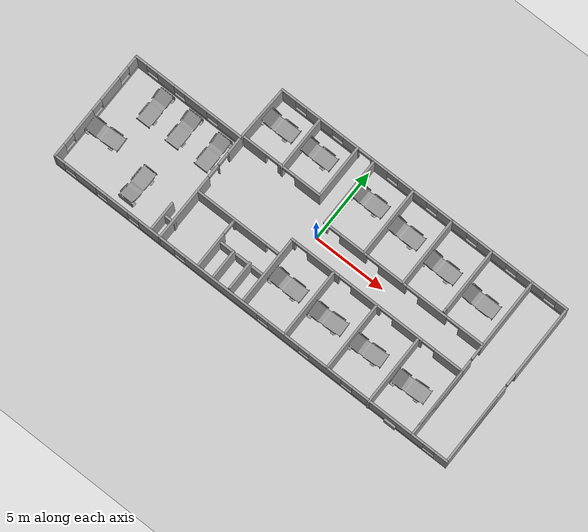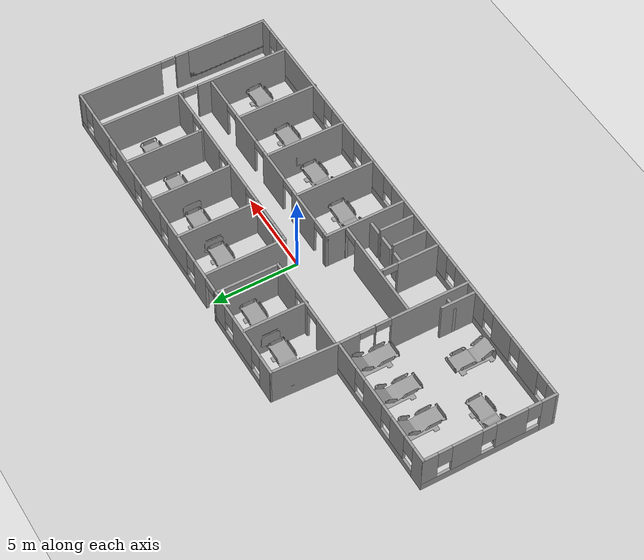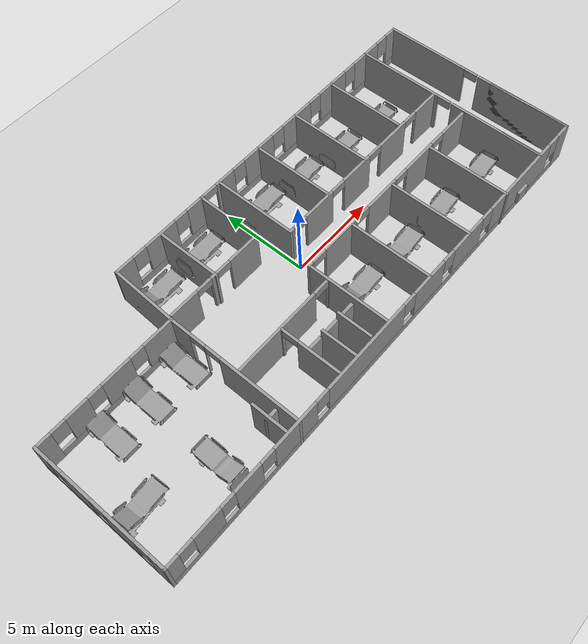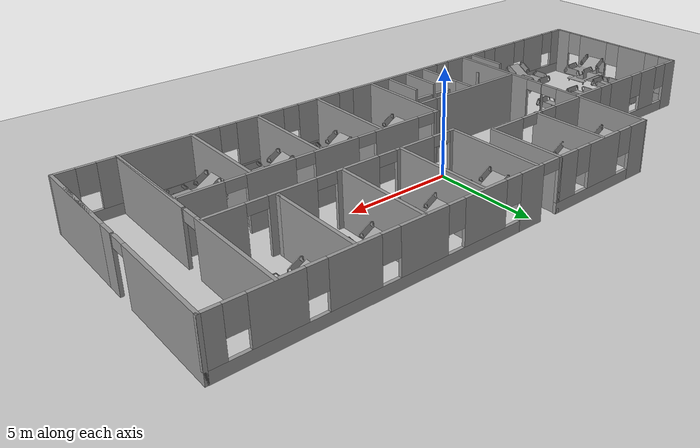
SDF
<sdf version="1.6">
 <world name="default">
  <light name="sun" type="directional">
   <pose>0 0 10 0 -0 0</pose>
   <diffuse>0.8 0.8 0.8 1</diffuse>
   <specular>0.1 0.1 0.1 1</specular>
   <attenuation>
    <range>1000</range>
    <constant>0.9</constant>
    <linear>0.01</linear>
    <quadratic>0.001</quadratic>
   </attenuation>
   <direction>-0.5 0.5 -1</direction>
  </light>
  <model name="ground_plane">
   <static>1</static>
   <link name="link">
    <collision name="collision">
     <geometry><plane><normal>0 0 1</normal><size>100 100</size></plane></geometry>
     <surface><friction><ode><mu>100</mu><mu2>50</mu2></ode></friction></surface>
    </collision>
    <visual name="visual">
     <cast_shadows>0</cast_shadows>
     <geometry><plane><normal>0 0 1</normal><size>100 100</size></plane></geometry>
     <material>
      <script><uri>file://media/materials/scripts/gazebo.material</uri><name>Gazebo/Grey</name></script>
     </material>
    </visual>
   </link>
  </model>
  <gravity>0 0 -9.8</gravity>
  <magnetic_field>6e-06 2.3e-05 -4.2e-05</magnetic_field>
  <atmosphere type="adiabatic"/>
  <physics name="default_physics" default="0" type="ode">
   <max_step_size>0.001</max_step_size>
   <real_time_factor>1</real_time_factor>
   <real_time_update_rate>1000</real_time_update_rate>
  </physics>
  <scene><ambient>0.4 0.4 0.4 1</ambient><background>0.7 0.7 0.7 1</background><shadows>1</shadows></scene>
  <spherical_coordinates>
   <surface_model>EARTH_WGS84</surface_model>
   <latitude_deg>0</latitude_deg>
   <longitude_deg>0</longitude_deg>
   <elevation>0</elevation>
   <heading_deg>0</heading_deg>
  </spherical_coordinates>
  <model name="hopial">
   <pose>-0.23473 -0.32757 0 0 -0 0</pose>
   <link name="Door_15">
    <collision name="Door_15_Collision">
     <geometry><box><size>0.9 0.17 2</size></box></geometry>
     <pose>0 0 1 0 -0 0</pose>
    </collision>
    <visual name="Door_15_Visual">
     <pose>0 0 1 0 -0 0</pose>
     <geometry><box><size>0.9 0.17 2</size></box></geometry>
     <material>
      <script><uri>file://media/materials/scripts/gazebo.material</uri><name>Gazebo/Grey</name></script>
     </material>
    </visual>
    <pose>-1.01365 -3.61001 0 0 -0 0</pose>
   </link>
   <link name="Door_16">
    <collision name="Door_16_Collision">
     <geometry><box><size>0.9 0.17 2</size></box></geometry>
     <pose>0 0 1 0 -0 0</pose>
    </collision>
    <visual name="Door_16_Visual">
     <pose>0 0 1 0 -0 0</pose>
     <geometry><box><size>0.9 0.17 2</size></box></geometry>
     <material>
      <script><uri>file://media/materials/scripts/gazebo.material</uri><name>Gazebo/Grey</name></script>
     </material>
    </visual>
    <pose>-3.33985 -3.61001 0 0 -0 0</pose>
   </link>
   <link name="Door_17">
    <collision name="Door_17_Collision">
     <geometry><box><size>0.9 0.17 2</size></box></geometry>
     <pose>0 0 1 0 -0 0</pose>
    </collision>
    <visual name="Door_17_Visual">
     <pose>0 0 1 0 -0 0</pose>
     <geometry><box><size>0.9 0.17 2</size></box></geometry>
     <material>
      <script><uri>file://media/materials/scripts/gazebo.material</uri><name>Gazebo/Grey</name></script>
     </material>
    </visual>
    <pose>-2.17675 -3.61001 0 0 -0 0</pose>
   </link>
   <link name="Door_18">
    <collision name="Door_18_Collision">
     <geometry><box><size>0.9 0.17 2</size></box></geometry>
     <pose>0 0 1 0 -0 0</pose>
    </collision>
    <visual name="Door_18_Visual">
     <pose>0 0 1 0 -0 0</pose>
     <geometry><box><size>0.9 0.17 2</size></box></geometry>
     <material>
      <script><uri>file://media/materials/scripts/gazebo.material</uri><name>Gazebo/Grey</name></script>
     </material>
    </visual>
    <pose>-7.01524 -4.40091 0 0 -0 0</pose>
   </link>
   <link name="Wall_0">
    <pose>4 5.69478 0 0 -0 0</pose>
    <visual name="Wall_0_Visual_0">
     <pose>-10.0664 0 1.25 0 -0 0</pose>
     <geometry><box><size>1.11724 0.15 2.5</size></box></geometry>
     <material>
      <script><uri>file://media/materials/scripts/gazebo.material</uri><name>Gazebo/Grey</name></script>
      <ambient>1 1 1 1</ambient>
     </material>
    </visual>
    <collision name="Wall_0_Collision_0">
     <geometry><box><size>1.11724 0.15 2.5</size></box></geometry>
     <pose>-10.0664 0 1.25 0 -0 0</pose>
    </collision>
    <visual name="Wall_0_Visual_1">
     <pose>-3.29053 0 1.25 0 -0 0</pose>
     <geometry><box><size>1.24358 0.15 2.5</size></box></geometry>
     <material>
      <script><uri>file://media/materials/scripts/gazebo.material</uri><name>Gazebo/Grey</name></script>
      <ambient>1 1 1 1</ambient>
     </material>
    </visual>
    <collision name="Wall_0_Collision_1">
     <geometry><box><size>1.24358 0.15 2.5</size></box></geometry>
     <pose>-3.29053 0 1.25 0 -0 0</pose>
    </collision>
    <visual name="Wall_0_Visual_2">
     <pose>-7.16004 0 0.25 0 -0 0</pose>
     <geometry><box><size>4.69544 0.15 0.5</size></box></geometry>
     <material>
      <script><uri>file://media/materials/scripts/gazebo.material</uri><name>Gazebo/Grey</name></script>
      <ambient>1 1 1 1</ambient>
     </material>
    </visual>
    <collision name="Wall_0_Collision_2">
     <geometry><box><size>4.69544 0.15 0.5</size></box></geometry>
     <pose>-7.16004 0 0.25 0 -0 0</pose>
    </collision>
    <visual name="Wall_0_Visual_3">
     <pose>3.97813 0 0.25 0 -0 0</pose>
     <geometry><box><size>13.2937 0.15 0.5</size></box></geometry>
     <material>
      <script><uri>file://media/materials/scripts/gazebo.material</uri><name>Gazebo/Grey</name></script>
      <ambient>1 1 1 1</ambient>
     </material>
    </visual>
    <collision name="Wall_0_Collision_3">
     <geometry><box><size>13.2937 0.15 0.5</size></box></geometry>
     <pose>3.97813 0 0.25 0 -0 0</pose>
    </collision>
    <visual name="Wall_0_Visual_4">
     <pose>-7.7353 0 1.5 0 -0 0</pose>
     <geometry><box><size>1.94491 0.15 2</size></box></geometry>
     <material>
      <script><uri>file://media/materials/scripts/gazebo.material</uri><name>Gazebo/Grey</name></script>
      <ambient>1 1 1 1</ambient>
     </material>
    </visual>
    <collision name="Wall_0_Collision_4">
     <geometry><box><size>1.94491 0.15 2</size></box></geometry>
     <pose>-7.7353 0 1.5 0 -0 0</pose>
    </collision>
    <visual name="Wall_0_Visual_5">
     <pose>-5.38758 0 1.5 0 -0 0</pose>
     <geometry><box><size>1.15053 0.15 2</size></box></geometry>
     <material>
      <script><uri>file://media/materials/scripts/gazebo.material</uri><name>Gazebo/Grey</name></script>
      <ambient>1 1 1 1</ambient>
     </material>
    </visual>
    <collision name="Wall_0_Collision_5">
     <geometry><box><size>1.15053 0.15 2</size></box></geometry>
     <pose>-5.38758 0 1.5 0 -0 0</pose>
    </collision>
    <visual name="Wall_0_Visual_6">
     <pose>-5.38758 0 1.5 0 -0 0</pose>
     <geometry><box><size>1.15053 0.15 2</size></box></geometry>
     <material>
      <script><uri>file://media/materials/scripts/gazebo.material</uri><name>Gazebo/Grey</name></script>
      <ambient>1 1 1 1</ambient>
     </material>
    </visual>
    <collision name="Wall_0_Collision_6">
     <geometry><box><size>1.15053 0.15 2</size></box></geometry>
     <pose>-5.38758 0 1.5 0 -0 0</pose>
    </collision>
    <visual name="Wall_0_Visual_7">
     <pose>-0.80324 0 1.5 0 -0 0</pose>
     <geometry><box><size>2.13101 0.15 2</size></box></geometry>
     <material>
      <script><uri>file://media/materials/scripts/gazebo.material</uri><name>Gazebo/Grey</name></script>
      <ambient>1 1 1 1</ambient>
     </material>
    </visual>
    <collision name="Wall_0_Collision_7">
     <geometry><box><size>2.13101 0.15 2</size></box></geometry>
     <pose>-0.80324 0 1.5 0 -0 0</pose>
    </collision>
    <visual name="Wall_0_Visual_8">
     <pose>2.15103 0 1.5 0 -0 0</pose>
     <geometry><box><size>2.17753 0.15 2</size></box></geometry>
     <material>
      <script><uri>file://media/materials/scripts/gazebo.material</uri><name>Gazebo/Grey</name></script>
      <ambient>1 1 1 1</ambient>
     </material>
    </visual>
    <collision name="Wall_0_Collision_8">
     <geometry><box><size>2.17753 0.15 2</size></box></geometry>
     <pose>2.15103 0 1.5 0 -0 0</pose>
    </collision>
    <visual name="Wall_0_Visual_9">
     <pose>5.1053 0 1.5 0 -0 0</pose>
     <geometry><box><size>2.13101 0.15 2</size></box></geometry>
     <material>
      <script><uri>file://media/materials/scripts/gazebo.material</uri><name>Gazebo/Grey</name></script>
      <ambient>1 1 1 1</ambient>
     </material>
    </visual>
    <collision name="Wall_0_Collision_9">
     <geometry><box><size>2.13101 0.15 2</size></box></geometry>
     <pose>5.1053 0 1.5 0 -0 0</pose>
    </collision>
    <visual name="Wall_0_Visual_10">
     <pose>7.98978 0 1.5 0 -0 0</pose>
     <geometry><box><size>2.03796 0.15 2</size></box></geometry>
     <material>
      <script><uri>file://media/materials/scripts/gazebo.material</uri><name>Gazebo/Grey</name></script>
      <ambient>1 1 1 1</ambient>
     </material>
    </visual>
    <collision name="Wall_0_Collision_10">
     <geometry><box><size>2.03796 0.15 2</size></box></geometry>
     <pose>7.98978 0 1.5 0 -0 0</pose>
    </collision>
    <visual name="Wall_0_Visual_11">
     <pose>10.2169 0 1.5 0 -0 0</pose>
     <geometry><box><size>0.816241 0.15 2</size></box></geometry>
     <material>
      <script><uri>file://media/materials/scripts/gazebo.material</uri><name>Gazebo/Grey</name></script>
      <ambient>1 1 1 1</ambient>
     </material>
    </visual>
    <collision name="Wall_0_Collision_11">
     <geometry><box><size>0.816241 0.15 2</size></box></geometry>
     <pose>10.2169 0 1.5 0 -0 0</pose>
    </collision>
    <visual name="Wall_0_Visual_12">
     <pose>-9.10776 0 1.9 0 -0 0</pose>
     <geometry><box><size>0.8 0.15 1.2</size></box></geometry>
     <material>
      <script><uri>file://media/materials/scripts/gazebo.material</uri><name>Gazebo/Grey</name></script>
      <ambient>1 1 1 1</ambient>
     </material>
    </visual>
    <collision name="Wall_0_Collision_12">
     <geometry><box><size>0.8 0.15 1.2</size></box></geometry>
     <pose>-9.10776 0 1.9 0 -0 0</pose>
    </collision>
    <visual name="Wall_0_Visual_13">
     <pose>-2.26874 0 1.9 0 -0 0</pose>
     <geometry><box><size>0.8 0.15 1.2</size></box></geometry>
     <material>
      <script><uri>file://media/materials/scripts/gazebo.material</uri><name>Gazebo/Grey</name></script>
      <ambient>1 1 1 1</ambient>
     </material>
    </visual>
    <collision name="Wall_0_Collision_13">
     <geometry><box><size>0.8 0.15 1.2</size></box></geometry>
     <pose>-2.26874 0 1.9 0 -0 0</pose>
    </collision>
    <visual name="Wall_0_Visual_14">
     <pose>-6.36285 0 1.9 0 -0 0</pose>
     <geometry><box><size>0.8 0.15 1.2</size></box></geometry>
     <material>
      <script><uri>file://media/materials/scripts/gazebo.material</uri><name>Gazebo/Grey</name></script>
      <ambient>1 1 1 1</ambient>
     </material>
    </visual>
    <collision name="Wall_0_Collision_14">
     <geometry><box><size>0.8 0.15 1.2</size></box></geometry>
     <pose>-6.36285 0 1.9 0 -0 0</pose>
    </collision>
    <visual name="Wall_0_Visual_15">
     <pose>0.662263 0 1.9 0 -0 0</pose>
     <geometry><box><size>0.8 0.15 1.2</size></box></geometry>
     <material>
      <script><uri>file://media/materials/scripts/gazebo.material</uri><name>Gazebo/Grey</name></script>
      <ambient>1 1 1 1</ambient>
     </material>
    </visual>
    <collision name="Wall_0_Collision_15">
     <geometry><box><size>0.8 0.15 1.2</size></box></geometry>
     <pose>0.662263 0 1.9 0 -0 0</pose>
    </collision>
    <visual name="Wall_0_Visual_16">
     <pose>3.63979 0 1.9 0 -0 0</pose>
     <geometry><box><size>0.8 0.15 1.2</size></box></geometry>
     <material>
      <script><uri>file://media/materials/scripts/gazebo.material</uri><name>Gazebo/Grey</name></script>
      <ambient>1 1 1 1</ambient>
     </material>
    </visual>
    <collision name="Wall_0_Collision_16">
     <geometry><box><size>0.8 0.15 1.2</size></box></geometry>
     <pose>3.63979 0 1.9 0 -0 0</pose>
    </collision>
    <visual name="Wall_0_Visual_17">
     <pose>6.5708 0 1.9 0 -0 0</pose>
     <geometry><box><size>0.8 0.15 1.2</size></box></geometry>
     <material>
      <script><uri>file://media/materials/scripts/gazebo.material</uri><name>Gazebo/Grey</name></script>
      <ambient>1 1 1 1</ambient>
     </material>
    </visual>
    <collision name="Wall_0_Collision_17">
     <geometry><box><size>0.8 0.15 1.2</size></box></geometry>
     <pose>6.5708 0 1.9 0 -0 0</pose>
    </collision>
    <visual name="Wall_0_Visual_18">
     <pose>9.40876 0 1.9 0 -0 0</pose>
     <geometry><box><size>0.8 0.15 1.2</size></box></geometry>
     <material>
      <script><uri>file://media/materials/scripts/gazebo.material</uri><name>Gazebo/Grey</name></script>
      <ambient>1 1 1 1</ambient>
     </material>
    </visual>
    <collision name="Wall_0_Collision_18">
     <geometry><box><size>0.8 0.15 1.2</size></box></geometry>
     <pose>9.40876 0 1.9 0 -0 0</pose>
    </collision>
    <visual name="Wall_0_Visual_19">
     <pose>-4.36232 0 2.25 0 -0 0</pose>
     <geometry><box><size>0.9 0.15 0.5</size></box></geometry>
     <material>
      <script><uri>file://media/materials/scripts/gazebo.material</uri><name>Gazebo/Grey</name></script>
      <ambient>1 1 1 1</ambient>
     </material>
    </visual>
    <collision name="Wall_0_Collision_19">
     <geometry><box><size>0.9 0.15 0.5</size></box></geometry>
     <pose>-4.36232 0 2.25 0 -0 0</pose>
    </collision>
    <visual name="Wall_0_Visual_20">
     <pose>-4.36232 0 2.25 0 -0 0</pose>
     <geometry><box><size>0.9 0.15 0.5</size></box></geometry>
     <material>
      <script><uri>file://media/materials/scripts/gazebo.material</uri><name>Gazebo/Grey</name></script>
      <ambient>1 1 1 1</ambient>
     </material>
    </visual>
    <collision name="Wall_0_Collision_20">
     <geometry><box><size>0.9 0.15 0.5</size></box></geometry>
     <pose>-4.36232 0 2.25 0 -0 0</pose>
    </collision>
   </link>
   <link name="Wall_1">
    <pose>14.55 0.019777 0 0 0 -1.5708</pose>
    <visual name="Wall_1_Visual_0">
     <pose>-3.26238 0 1.25 0 -0 0</pose>
     <geometry><box><size>4.97525 0.15 2.5</size></box></geometry>
     <material>
      <script><uri>file://media/materials/scripts/gazebo.material</uri><name>Gazebo/Grey</name></script>
      <ambient>1 1 1 1</ambient>
     </material>
    </visual>
    <collision name="Wall_1_Collision_0">
     <geometry><box><size>4.97525 0.15 2.5</size></box></geometry>
     <pose>-3.26238 0 1.25 0 -0 0</pose>
    </collision>
    <visual name="Wall_1_Visual_1">
     <pose>2.93763 0 1.25 0 -0 0</pose>
     <geometry><box><size>5.62475 0.15 2.5</size></box></geometry>
     <material>
      <script><uri>file://media/materials/scripts/gazebo.material</uri><name>Gazebo/Grey</name></script>
      <ambient>1 1 1 1</ambient>
     </material>
    </visual>
    <collision name="Wall_1_Collision_1">
     <geometry><box><size>5.62475 0.15 2.5</size></box></geometry>
     <pose>2.93763 0 1.25 0 -0 0</pose>
    </collision>
    <visual name="Wall_1_Visual_2">
     <pose>3.33308 0 1.25 0 -0 0</pose>
     <geometry><box><size>4.83384 0.15 2.5</size></box></geometry>
     <material>
      <script><uri>file://media/materials/scripts/gazebo.material</uri><name>Gazebo/Grey</name></script>
      <ambient>1 1 1 1</ambient>
     </material>
    </visual>
    <collision name="Wall_1_Collision_2">
     <geometry><box><size>4.83384 0.15 2.5</size></box></geometry>
     <pose>3.33308 0 1.25 0 -0 0</pose>
    </collision>
    <visual name="Wall_1_Visual_3">
     <pose>-0.379297 0 2.25 0 -0 0</pose>
     <geometry><box><size>0.790907 0.15 0.5</size></box></geometry>
     <material>
      <script><uri>file://media/materials/scripts/gazebo.material</uri><name>Gazebo/Grey</name></script>
      <ambient>1 1 1 1</ambient>
     </material>
    </visual>
    <collision name="Wall_1_Collision_3">
     <geometry><box><size>0.790907 0.15 0.5</size></box></geometry>
     <pose>-0.379297 0 2.25 0 -0 0</pose>
    </collision>
   </link>
   <link name="Wall_11">
    <collision name="Wall_11_Collision">
     <geometry><box><size>2 0.15 2.5</size></box></geometry>
     <pose>0 0 1.25 0 -0 0</pose>
    </collision>
    <visual name="Wall_11_Visual">
     <pose>0 0 1.25 0 -0 0</pose>
     <geometry><box><size>2 0.15 2.5</size></box></geometry>
     <material>
      <script><uri>file://media/materials/scripts/gazebo.material</uri><name>Gazebo/Grey</name></script>
      <ambient>1 1 1 1</ambient>
     </material>
    </visual>
    <pose>-7.38743 -4.58153 0 0 0 -1.5708</pose>
   </link>
   <link name="Wall_13">
    <collision name="Wall_13_Collision">
     <geometry><box><size>3.75 0.15 2.5</size></box></geometry>
     <pose>0 0 1.25 0 -0 0</pose>
    </collision>
    <visual name="Wall_13_Visual">
     <pose>0 0 1.25 0 -0 0</pose>
     <geometry><box><size>3.75 0.15 2.5</size></box></geometry>
     <material>
      <script><uri>file://media/materials/scripts/gazebo.material</uri><name>Gazebo/Grey</name></script>
      <ambient>1 1 1 1</ambient>
     </material>
    </visual>
    <pose>-0.920607 3.89478 0 0 0 -1.5708</pose>
   </link>
   <link name="Wall_14">
    <pose>-3.72061 2.09478 0 0 -0 3.14159</pose>
    <visual name="Wall_14_Visual_0">
     <pose>-1.92266 0 1.25 0 -0 0</pose>
     <geometry><box><size>1.90467 0.15 2.5</size></box></geometry>
     <material>
      <script><uri>file://media/materials/scripts/gazebo.material</uri><name>Gazebo/Grey</name></script>
      <ambient>1 1 1 1</ambient>
     </material>
    </visual>
    <collision name="Wall_14_Collision_0">
     <geometry><box><size>1.90467 0.15 2.5</size></box></geometry>
     <pose>-1.92266 0 1.25 0 -0 0</pose>
    </collision>
    <visual name="Wall_14_Visual_1">
     <pose>0.107745 0 1.25 0 -0 0</pose>
     <geometry><box><size>0.356146 0.15 2.5</size></box></geometry>
     <material>
      <script><uri>file://media/materials/scripts/gazebo.material</uri><name>Gazebo/Grey</name></script>
      <ambient>1 1 1 1</ambient>
     </material>
    </visual>
    <collision name="Wall_14_Collision_1">
     <geometry><box><size>0.356146 0.15 2.5</size></box></geometry>
     <pose>0.107745 0 1.25 0 -0 0</pose>
    </collision>
    <visual name="Wall_14_Visual_2">
     <pose>2.03041 0 1.25 0 -0 0</pose>
     <geometry><box><size>1.68918 0.15 2.5</size></box></geometry>
     <material>
      <script><uri>file://media/materials/scripts/gazebo.material</uri><name>Gazebo/Grey</name></script>
      <ambient>1 1 1 1</ambient>
     </material>
    </visual>
    <collision name="Wall_14_Collision_2">
     <geometry><box><size>1.68918 0.15 2.5</size></box></geometry>
     <pose>2.03041 0 1.25 0 -0 0</pose>
    </collision>
    <visual name="Wall_14_Visual_3">
     <pose>-0.520328 0 2.25 0 -0 0</pose>
     <geometry><box><size>0.9 0.15 0.5</size></box></geometry>
     <material>
      <script><uri>file://media/materials/scripts/gazebo.material</uri><name>Gazebo/Grey</name></script>
      <ambient>1 1 1 1</ambient>
     </material>
    </visual>
    <collision name="Wall_14_Collision_3">
     <geometry><box><size>0.9 0.15 0.5</size></box></geometry>
     <pose>-0.520328 0 2.25 0 -0 0</pose>
    </collision>
    <visual name="Wall_14_Visual_4">
     <pose>0.735818 0 2.25 0 -0 0</pose>
     <geometry><box><size>0.9 0.15 0.5</size></box></geometry>
     <material>
      <script><uri>file://media/materials/scripts/gazebo.material</uri><name>Gazebo/Grey</name></script>
      <ambient>1 1 1 1</ambient>
     </material>
    </visual>
    <collision name="Wall_14_Collision_4">
     <geometry><box><size>0.9 0.15 0.5</size></box></geometry>
     <pose>0.735818 0 2.25 0 -0 0</pose>
    </collision>
   </link>
   <link name="Wall_16">
    <collision name="Wall_16_Collision">
     <geometry><box><size>3.75 0.15 2.5</size></box></geometry>
     <pose>0 0 1.25 0 -0 0</pose>
    </collision>
    <visual name="Wall_16_Visual">
     <pose>0 0 1.25 0 -0 0</pose>
     <geometry><box><size>3.75 0.15 2.5</size></box></geometry>
     <material>
      <script><uri>file://media/materials/scripts/gazebo.material</uri><name>Gazebo/Grey</name></script>
      <ambient>1 1 1 1</ambient>
     </material>
    </visual>
    <pose>-3.71204 3.84825 0 0 0 -1.5708</pose>
   </link>
   <link name="Wall_18">
    <collision name="Wall_18_Collision">
     <geometry><box><size>4.75 0.15 2.5</size></box></geometry>
     <pose>0 0 1.25 0 -0 0</pose>
    </collision>
    <visual name="Wall_18_Visual">
     <pose>0 0 1.25 0 -0 0</pose>
     <geometry><box><size>4.75 0.15 2.5</size></box></geometry>
     <material>
      <script><uri>file://media/materials/scripts/gazebo.material</uri><name>Gazebo/Grey</name></script>
      <ambient>1 1 1 1</ambient>
     </material>
    </visual>
    <pose>0.335539 3.30173 0 0 0 -1.5708</pose>
   </link>
   <link name="Wall_19">
    <pose>6.13554 1.00173 0 0 -0 0</pose>
    <visual name="Wall_19_Visual_0">
     <pose>-5.71357 0 1.25 0 -0 0</pose>
     <geometry><box><size>0.322859 0.15 2.5</size></box></geometry>
     <material>
      <script><uri>file://media/materials/scripts/gazebo.material</uri><name>Gazebo/Grey</name></script>
      <ambient>1 1 1 1</ambient>
     </material>
    </visual>
    <collision name="Wall_19_Collision_0">
     <geometry><box><size>0.322859 0.15 2.5</size></box></geometry>
     <pose>-5.71357 0 1.25 0 -0 0</pose>
    </collision>
    <visual name="Wall_19_Visual_1">
     <pose>-3.6599 0 1.25 0 -0 0</pose>
     <geometry><box><size>1.98448 0.15 2.5</size></box></geometry>
     <material>
      <script><uri>file://media/materials/scripts/gazebo.material</uri><name>Gazebo/Grey</name></script>
      <ambient>1 1 1 1</ambient>
     </material>
    </visual>
    <collision name="Wall_19_Collision_1">
     <geometry><box><size>1.98448 0.15 2.5</size></box></geometry>
     <pose>-3.6599 0 1.25 0 -0 0</pose>
    </collision>
    <visual name="Wall_19_Visual_2">
     <pose>-0.752155 0 1.25 0 -0 0</pose>
     <geometry><box><size>2.03101 0.15 2.5</size></box></geometry>
     <material>
      <script><uri>file://media/materials/scripts/gazebo.material</uri><name>Gazebo/Grey</name></script>
      <ambient>1 1 1 1</ambient>
     </material>
    </visual>
    <collision name="Wall_19_Collision_2">
     <geometry><box><size>2.03101 0.15 2.5</size></box></geometry>
     <pose>-0.752155 0 1.25 0 -0 0</pose>
    </collision>
    <visual name="Wall_19_Visual_3">
     <pose>2.20211 0 1.25 0 -0 0</pose>
     <geometry><box><size>2.07753 0.15 2.5</size></box></geometry>
     <material>
      <script><uri>file://media/materials/scripts/gazebo.material</uri><name>Gazebo/Grey</name></script>
      <ambient>1 1 1 1</ambient>
     </material>
    </visual>
    <collision name="Wall_19_Collision_3">
     <geometry><box><size>2.07753 0.15 2.5</size></box></geometry>
     <pose>2.20211 0 1.25 0 -0 0</pose>
    </collision>
    <visual name="Wall_19_Visual_4">
     <pose>5.00794 0 1.25 0 -0 0</pose>
     <geometry><box><size>1.73412 0.15 2.5</size></box></geometry>
     <material>
      <script><uri>file://media/materials/scripts/gazebo.material</uri><name>Gazebo/Grey</name></script>
      <ambient>1 1 1 1</ambient>
     </material>
    </visual>
    <collision name="Wall_19_Collision_4">
     <geometry><box><size>1.73412 0.15 2.5</size></box></geometry>
     <pose>5.00794 0 1.25 0 -0 0</pose>
    </collision>
    <visual name="Wall_19_Visual_5">
     <pose>-5.10214 0 2.25 0 -0 0</pose>
     <geometry><box><size>0.9 0.15 0.5</size></box></geometry>
     <material>
      <script><uri>file://media/materials/scripts/gazebo.material</uri><name>Gazebo/Grey</name></script>
      <ambient>1 1 1 1</ambient>
     </material>
    </visual>
    <collision name="Wall_19_Collision_5">
     <geometry><box><size>0.9 0.15 0.5</size></box></geometry>
     <pose>-5.10214 0 2.25 0 -0 0</pose>
    </collision>
    <visual name="Wall_19_Visual_6">
     <pose>-2.21766 0 2.25 0 -0 0</pose>
     <geometry><box><size>0.9 0.15 0.5</size></box></geometry>
     <material>
      <script><uri>file://media/materials/scripts/gazebo.material</uri><name>Gazebo/Grey</name></script>
      <ambient>1 1 1 1</ambient>
     </material>
    </visual>
    <collision name="Wall_19_Collision_6">
     <geometry><box><size>0.9 0.15 0.5</size></box></geometry>
     <pose>-2.21766 0 2.25 0 -0 0</pose>
    </collision>
    <visual name="Wall_19_Visual_7">
     <pose>0.713348 0 2.25 0 -0 0</pose>
     <geometry><box><size>0.9 0.15 0.5</size></box></geometry>
     <material>
      <script><uri>file://media/materials/scripts/gazebo.material</uri><name>Gazebo/Grey</name></script>
      <ambient>1 1 1 1</ambient>
     </material>
    </visual>
    <collision name="Wall_19_Collision_7">
     <geometry><box><size>0.9 0.15 0.5</size></box></geometry>
     <pose>0.713348 0 2.25 0 -0 0</pose>
    </collision>
    <visual name="Wall_19_Visual_8">
     <pose>3.69088 0 2.25 0 -0 0</pose>
     <geometry><box><size>0.9 0.15 0.5</size></box></geometry>
     <material>
      <script><uri>file://media/materials/scripts/gazebo.material</uri><name>Gazebo/Grey</name></script>
      <ambient>1 1 1 1</ambient>
     </material>
    </visual>
    <collision name="Wall_19_Collision_8">
     <geometry><box><size>0.9 0.15 0.5</size></box></geometry>
     <pose>3.69088 0 2.25 0 -0 0</pose>
    </collision>
   </link>
   <link name="Wall_2">
    <pose>0 -5.65522 0 0 -0 3.14159</pose>
    <visual name="Wall_2_Visual_0">
     <pose>-14.1471 0 1.25 0 -0 0</pose>
     <geometry><box><size>0.955813 0.15 2.5</size></box></geometry>
     <material>
      <script><uri>file://media/materials/scripts/gazebo.material</uri><name>Gazebo/Grey</name></script>
      <ambient>1 1 1 1</ambient>
     </material>
    </visual>
    <collision name="Wall_2_Collision_0">
     <geometry><box><size>0.955813 0.15 2.5</size></box></geometry>
     <pose>-14.1471 0 1.25 0 -0 0</pose>
    </collision>
    <visual name="Wall_2_Visual_1">
     <pose>0.477906 0 0.25 0 -0 0</pose>
     <geometry><box><size>28.2942 0.15 0.5</size></box></geometry>
     <material>
      <script><uri>file://media/materials/scripts/gazebo.material</uri><name>Gazebo/Grey</name></script>
      <ambient>1 1 1 1</ambient>
     </material>
    </visual>
    <collision name="Wall_2_Collision_1">
     <geometry><box><size>28.2942 0.15 0.5</size></box></geometry>
     <pose>0.477906 0 0.25 0 -0 0</pose>
    </collision>
    <visual name="Wall_2_Visual_2">
     <pose>-10.2451 0 1.5 0 -0 0</pose>
     <geometry><box><size>5.24811 0.15 2</size></box></geometry>
     <material>
      <script><uri>file://media/materials/scripts/gazebo.material</uri><name>Gazebo/Grey</name></script>
      <ambient>1 1 1 1</ambient>
     </material>
    </visual>
    <collision name="Wall_2_Collision_2">
     <geometry><box><size>5.24811 0.15 2</size></box></geometry>
     <pose>-10.2451 0 1.5 0 -0 0</pose>
    </collision>
    <visual name="Wall_2_Visual_3">
     <pose>-5.63926 0 1.5 0 -0 0</pose>
     <geometry><box><size>2.36363 0.15 2</size></box></geometry>
     <material>
      <script><uri>file://media/materials/scripts/gazebo.material</uri><name>Gazebo/Grey</name></script>
      <ambient>1 1 1 1</ambient>
     </material>
    </visual>
    <collision name="Wall_2_Collision_3">
     <geometry><box><size>2.36363 0.15 2</size></box></geometry>
     <pose>-5.63926 0 1.5 0 -0 0</pose>
    </collision>
    <visual name="Wall_2_Visual_4">
     <pose>-2.52216 0 1.5 0 -0 0</pose>
     <geometry><box><size>2.27058 0.15 2</size></box></geometry>
     <material>
      <script><uri>file://media/materials/scripts/gazebo.material</uri><name>Gazebo/Grey</name></script>
      <ambient>1 1 1 1</ambient>
     </material>
    </visual>
    <collision name="Wall_2_Collision_4">
     <geometry><box><size>2.27058 0.15 2</size></box></geometry>
     <pose>-2.52216 0 1.5 0 -0 0</pose>
    </collision>
    <visual name="Wall_2_Visual_5">
     <pose>2.10697 0 1.5 0 -0 0</pose>
     <geometry><box><size>5.38768 0.15 2</size></box></geometry>
     <material>
      <script><uri>file://media/materials/scripts/gazebo.material</uri><name>Gazebo/Grey</name></script>
      <ambient>1 1 1 1</ambient>
     </material>
    </visual>
    <collision name="Wall_2_Collision_5">
     <geometry><box><size>5.38768 0.15 2</size></box></geometry>
     <pose>2.10697 0 1.5 0 -0 0</pose>
    </collision>
    <visual name="Wall_2_Visual_6">
     <pose>6.94545 0 1.5 0 -0 0</pose>
     <geometry><box><size>2.68929 0.15 2</size></box></geometry>
     <material>
      <script><uri>file://media/materials/scripts/gazebo.material</uri><name>Gazebo/Grey</name></script>
      <ambient>1 1 1 1</ambient>
     </material>
    </visual>
    <collision name="Wall_2_Collision_6">
     <geometry><box><size>2.68929 0.15 2</size></box></geometry>
     <pose>6.94545 0 1.5 0 -0 0</pose>
    </collision>
    <visual name="Wall_2_Visual_7">
     <pose>9.87646 0 1.5 0 -0 0</pose>
     <geometry><box><size>1.57272 0.15 2</size></box></geometry>
     <material>
      <script><uri>file://media/materials/scripts/gazebo.material</uri><name>Gazebo/Grey</name></script>
      <ambient>1 1 1 1</ambient>
     </material>
    </visual>
    <collision name="Wall_2_Collision_7">
     <geometry><box><size>1.57272 0.15 2</size></box></geometry>
     <pose>9.87646 0 1.5 0 -0 0</pose>
    </collision>
    <visual name="Wall_2_Visual_8">
     <pose>12.2492 0 1.5 0 -0 0</pose>
     <geometry><box><size>1.57272 0.15 2</size></box></geometry>
     <material>
      <script><uri>file://media/materials/scripts/gazebo.material</uri><name>Gazebo/Grey</name></script>
      <ambient>1 1 1 1</ambient>
     </material>
    </visual>
    <collision name="Wall_2_Collision_8">
     <geometry><box><size>1.57272 0.15 2</size></box></geometry>
     <pose>12.2492 0 1.5 0 -0 0</pose>
    </collision>
    <visual name="Wall_2_Visual_9">
     <pose>14.2303 0 1.5 0 -0 0</pose>
     <geometry><box><size>0.789461 0.15 2</size></box></geometry>
     <material>
      <script><uri>file://media/materials/scripts/gazebo.material</uri><name>Gazebo/Grey</name></script>
      <ambient>1 1 1 1</ambient>
     </material>
    </visual>
    <collision name="Wall_2_Collision_9">
     <geometry><box><size>0.789461 0.15 2</size></box></geometry>
     <pose>14.2303 0 1.5 0 -0 0</pose>
    </collision>
    <visual name="Wall_2_Visual_10">
     <pose>-13.2692 0 1.9 0 -0 0</pose>
     <geometry><box><size>0.8 0.15 1.2</size></box></geometry>
     <material>
      <script><uri>file://media/materials/scripts/gazebo.material</uri><name>Gazebo/Grey</name></script>
      <ambient>1 1 1 1</ambient>
     </material>
    </visual>
    <collision name="Wall_2_Collision_10">
     <geometry><box><size>0.8 0.15 1.2</size></box></geometry>
     <pose>-13.2692 0 1.9 0 -0 0</pose>
    </collision>
    <visual name="Wall_2_Visual_11">
     <pose>-7.22108 0 1.9 0 -0 0</pose>
     <geometry><box><size>0.8 0.15 1.2</size></box></geometry>
     <material>
      <script><uri>file://media/materials/scripts/gazebo.material</uri><name>Gazebo/Grey</name></script>
      <ambient>1 1 1 1</ambient>
     </material>
    </visual>
    <collision name="Wall_2_Collision_11">
     <geometry><box><size>0.8 0.15 1.2</size></box></geometry>
     <pose>-7.22108 0 1.9 0 -0 0</pose>
    </collision>
    <visual name="Wall_2_Visual_12">
     <pose>-4.05745 0 1.9 0 -0 0</pose>
     <geometry><box><size>0.8 0.15 1.2</size></box></geometry>
     <material>
      <script><uri>file://media/materials/scripts/gazebo.material</uri><name>Gazebo/Grey</name></script>
      <ambient>1 1 1 1</ambient>
     </material>
    </visual>
    <collision name="Wall_2_Collision_12">
     <geometry><box><size>0.8 0.15 1.2</size></box></geometry>
     <pose>-4.05745 0 1.9 0 -0 0</pose>
    </collision>
    <visual name="Wall_2_Visual_13">
     <pose>-0.986874 0 1.9 0 -0 0</pose>
     <geometry><box><size>0.8 0.15 1.2</size></box></geometry>
     <material>
      <script><uri>file://media/materials/scripts/gazebo.material</uri><name>Gazebo/Grey</name></script>
      <ambient>1 1 1 1</ambient>
     </material>
    </visual>
    <collision name="Wall_2_Collision_13">
     <geometry><box><size>0.8 0.15 1.2</size></box></geometry>
     <pose>-0.986874 0 1.9 0 -0 0</pose>
    </collision>
    <visual name="Wall_2_Visual_14">
     <pose>5.20081 0 1.9 0 -0 0</pose>
     <geometry><box><size>0.8 0.15 1.2</size></box></geometry>
     <material>
      <script><uri>file://media/materials/scripts/gazebo.material</uri><name>Gazebo/Grey</name></script>
      <ambient>1 1 1 1</ambient>
     </material>
    </visual>
    <collision name="Wall_2_Collision_14">
     <geometry><box><size>0.8 0.15 1.2</size></box></geometry>
     <pose>5.20081 0 1.9 0 -0 0</pose>
    </collision>
    <visual name="Wall_2_Visual_15">
     <pose>8.6901 0 1.9 0 -0 0</pose>
     <geometry><box><size>0.8 0.15 1.2</size></box></geometry>
     <material>
      <script><uri>file://media/materials/scripts/gazebo.material</uri><name>Gazebo/Grey</name></script>
      <ambient>1 1 1 1</ambient>
     </material>
    </visual>
    <collision name="Wall_2_Collision_15">
     <geometry><box><size>0.8 0.15 1.2</size></box></geometry>
     <pose>8.6901 0 1.9 0 -0 0</pose>
    </collision>
    <visual name="Wall_2_Visual_16">
     <pose>11.0628 0 1.9 0 -0 0</pose>
     <geometry><box><size>0.8 0.15 1.2</size></box></geometry>
     <material>
      <script><uri>file://media/materials/scripts/gazebo.material</uri><name>Gazebo/Grey</name></script>
      <ambient>1 1 1 1</ambient>
     </material>
    </visual>
    <collision name="Wall_2_Collision_16">
     <geometry><box><size>0.8 0.15 1.2</size></box></geometry>
     <pose>11.0628 0 1.9 0 -0 0</pose>
    </collision>
    <visual name="Wall_2_Visual_17">
     <pose>13.4355 0 1.9 0 -0 0</pose>
     <geometry><box><size>0.8 0.15 1.2</size></box></geometry>
     <material>
      <script><uri>file://media/materials/scripts/gazebo.material</uri><name>Gazebo/Grey</name></script>
      <ambient>1 1 1 1</ambient>
     </material>
    </visual>
    <collision name="Wall_2_Collision_17">
     <geometry><box><size>0.8 0.15 1.2</size></box></geometry>
     <pose>13.4355 0 1.9 0 -0 0</pose>
    </collision>
   </link>
   <link name="Wall_21">
    <pose>-3.625 -2.12124 0 0 -0 0</pose>
    <visual name="Wall_21_Visual_0">
     <pose>-0.465851 0 1.25 0 -0 0</pose>
     <geometry><box><size>5.0683 0.15 2.5</size></box></geometry>
     <material>
      <script><uri>file://media/materials/scripts/gazebo.material</uri><name>Gazebo/Grey</name></script>
      <ambient>1 1 1 1</ambient>
     </material>
    </visual>
    <collision name="Wall_21_Collision_0">
     <geometry><box><size>5.0683 0.15 2.5</size></box></geometry>
     <pose>-0.465851 0 1.25 0 -0 0</pose>
    </collision>
    <visual name="Wall_21_Visual_1">
     <pose>2.98415 0 1.25 0 -0 0</pose>
     <geometry><box><size>0.031702 0.15 2.5</size></box></geometry>
     <material>
      <script><uri>file://media/materials/scripts/gazebo.material</uri><name>Gazebo/Grey</name></script>
      <ambient>1 1 1 1</ambient>
     </material>
    </visual>
    <collision name="Wall_21_Collision_1">
     <geometry><box><size>0.031702 0.15 2.5</size></box></geometry>
     <pose>2.98415 0 1.25 0 -0 0</pose>
    </collision>
    <visual name="Wall_21_Visual_2">
     <pose>2.5183 0 2.25 0 -0 0</pose>
     <geometry><box><size>0.9 0.15 0.5</size></box></geometry>
     <material>
      <script><uri>file://media/materials/scripts/gazebo.material</uri><name>Gazebo/Grey</name></script>
      <ambient>1 1 1 1</ambient>
     </material>
    </visual>
    <collision name="Wall_21_Collision_2">
     <geometry><box><size>0.9 0.15 0.5</size></box></geometry>
     <pose>2.5183 0 2.25 0 -0 0</pose>
    </collision>
   </link>
   <link name="Wall_23">
    <collision name="Wall_23_Collision">
     <geometry><box><size>4.75 0.15 2.5</size></box></geometry>
     <pose>0 0 1.25 0 -0 0</pose>
    </collision>
    <visual name="Wall_23_Visual">
     <pose>0 0 1.25 0 -0 0</pose>
     <geometry><box><size>4.75 0.15 2.5</size></box></geometry>
     <material>
      <script><uri>file://media/materials/scripts/gazebo.material</uri><name>Gazebo/Grey</name></script>
      <ambient>1 1 1 1</ambient>
     </material>
    </visual>
    <pose>-0.548415 -3.25814 0 0 0 -1.5708</pose>
   </link>
   <link name="Wall_25">
    <collision name="Wall_25_Collision">
     <geometry><box><size>2 0.15 2.5</size></box></geometry>
     <pose>0 0 1.25 0 -0 0</pose>
    </collision>
    <visual name="Wall_25_Visual">
     <pose>0 0 1.25 0 -0 0</pose>
     <geometry><box><size>2 0.15 2.5</size></box></geometry>
     <material>
      <script><uri>file://media/materials/scripts/gazebo.material</uri><name>Gazebo/Grey</name></script>
      <ambient>1 1 1 1</ambient>
     </material>
    </visual>
    <pose>-1.61847 -4.53501 0 0 0 -1.5708</pose>
   </link>
   <link name="Wall_28">
    <collision name="Wall_28_Collision">
     <geometry><box><size>2 0.15 2.5</size></box></geometry>
     <pose>0 0 1.25 0 -0 0</pose>
    </collision>
    <visual name="Wall_28_Visual">
     <pose>0 0 1.25 0 -0 0</pose>
     <geometry><box><size>2 0.15 2.5</size></box></geometry>
     <material>
      <script><uri>file://media/materials/scripts/gazebo.material</uri><name>Gazebo/Grey</name></script>
      <ambient>1 1 1 1</ambient>
     </material>
    </visual>
    <pose>-2.78156 -4.58153 0 0 0 -1.5708</pose>
   </link>
   <link name="Wall_3">
    <pose>-14.55 -1.85522 0 0 -0 1.5708</pose>
    <visual name="Wall_3_Visual_0">
     <pose>-3.41034 0 1.25 0 -0 0</pose>
     <geometry><box><size>0.929311 0.15 2.5</size></box></geometry>
     <material>
      <script><uri>file://media/materials/scripts/gazebo.material</uri><name>Gazebo/Grey</name></script>
      <ambient>1 1 1 1</ambient>
     </material>
    </visual>
    <collision name="Wall_3_Collision_0">
     <geometry><box><size>0.929311 0.15 2.5</size></box></geometry>
     <pose>-3.41034 0 1.25 0 -0 0</pose>
    </collision>
    <visual name="Wall_3_Visual_1">
     <pose>0.464655 0 0.25 0 -0 0</pose>
     <geometry><box><size>6.82069 0.15 0.5</size></box></geometry>
     <material>
      <script><uri>file://media/materials/scripts/gazebo.material</uri><name>Gazebo/Grey</name></script>
      <ambient>1 1 1 1</ambient>
     </material>
    </visual>
    <collision name="Wall_3_Collision_1">
     <geometry><box><size>6.82069 0.15 0.5</size></box></geometry>
     <pose>0.464655 0 0.25 0 -0 0</pose>
    </collision>
    <visual name="Wall_3_Visual_2">
     <pose>-1.24302 0 1.5 0 -0 0</pose>
     <geometry><box><size>1.80534 0.15 2</size></box></geometry>
     <material>
      <script><uri>file://media/materials/scripts/gazebo.material</uri><name>Gazebo/Grey</name></script>
      <ambient>1 1 1 1</ambient>
     </material>
    </visual>
    <collision name="Wall_3_Collision_2">
     <geometry><box><size>1.80534 0.15 2</size></box></geometry>
     <pose>-1.24302 0 1.5 0 -0 0</pose>
    </collision>
    <visual name="Wall_3_Visual_3">
     <pose>1.3158 0 1.5 0 -0 0</pose>
     <geometry><box><size>1.71229 0.15 2</size></box></geometry>
     <material>
      <script><uri>file://media/materials/scripts/gazebo.material</uri><name>Gazebo/Grey</name></script>
      <ambient>1 1 1 1</ambient>
     </material>
    </visual>
    <collision name="Wall_3_Collision_3">
     <geometry><box><size>1.71229 0.15 2</size></box></geometry>
     <pose>1.3158 0 1.5 0 -0 0</pose>
    </collision>
    <visual name="Wall_3_Visual_4">
     <pose>3.42347 0 1.5 0 -0 0</pose>
     <geometry><box><size>0.903059 0.15 2</size></box></geometry>
     <material>
      <script><uri>file://media/materials/scripts/gazebo.material</uri><name>Gazebo/Grey</name></script>
      <ambient>1 1 1 1</ambient>
     </material>
    </visual>
    <collision name="Wall_3_Collision_4">
     <geometry><box><size>0.903059 0.15 2</size></box></geometry>
     <pose>3.42347 0 1.5 0 -0 0</pose>
    </collision>
    <visual name="Wall_3_Visual_5">
     <pose>-2.54569 0 1.9 0 -0 0</pose>
     <geometry><box><size>0.8 0.15 1.2</size></box></geometry>
     <material>
      <script><uri>file://media/materials/scripts/gazebo.material</uri><name>Gazebo/Grey</name></script>
      <ambient>1 1 1 1</ambient>
     </material>
    </visual>
    <collision name="Wall_3_Collision_5">
     <geometry><box><size>0.8 0.15 1.2</size></box></geometry>
     <pose>-2.54569 0 1.9 0 -0 0</pose>
    </collision>
    <visual name="Wall_3_Visual_6">
     <pose>0.05965 0 1.9 0 -0 0</pose>
     <geometry><box><size>0.8 0.15 1.2</size></box></geometry>
     <material>
      <script><uri>file://media/materials/scripts/gazebo.material</uri><name>Gazebo/Grey</name></script>
      <ambient>1 1 1 1</ambient>
     </material>
    </visual>
    <collision name="Wall_3_Collision_6">
     <geometry><box><size>0.8 0.15 1.2</size></box></geometry>
     <pose>0.05965 0 1.9 0 -0 0</pose>
    </collision>
    <visual name="Wall_3_Visual_7">
     <pose>2.57194 0 1.9 0 -0 0</pose>
     <geometry><box><size>0.8 0.15 1.2</size></box></geometry>
     <material>
      <script><uri>file://media/materials/scripts/gazebo.material</uri><name>Gazebo/Grey</name></script>
      <ambient>1 1 1 1</ambient>
     </material>
    </visual>
    <collision name="Wall_3_Collision_7">
     <geometry><box><size>0.8 0.15 1.2</size></box></geometry>
     <pose>2.57194 0 1.9 0 -0 0</pose>
    </collision>
   </link>
   <link name="Wall_30">
    <pose>-3.89814 -3.88929 0 0 0 -1.5708</pose>
    <visual name="Wall_30_Visual_0">
     <pose>-1.68162 0 1.25 0 -0 0</pose>
     <geometry><box><size>0.136763 0.15 2.5</size></box></geometry>
     <material>
      <script><uri>file://media/materials/scripts/gazebo.material</uri><name>Gazebo/Grey</name></script>
      <ambient>1 1 1 1</ambient>
     </material>
    </visual>
    <collision name="Wall_30_Collision_0">
     <geometry><box><size>0.136763 0.15 2.5</size></box></geometry>
     <pose>-1.68162 0 1.25 0 -0 0</pose>
    </collision>
    <visual name="Wall_30_Visual_1">
     <pose>0.518381 0 1.25 0 -0 0</pose>
     <geometry><box><size>2.46324 0.15 2.5</size></box></geometry>
     <material>
      <script><uri>file://media/materials/scripts/gazebo.material</uri><name>Gazebo/Grey</name></script>
      <ambient>1 1 1 1</ambient>
     </material>
    </visual>
    <collision name="Wall_30_Collision_1">
     <geometry><box><size>2.46324 0.15 2.5</size></box></geometry>
     <pose>0.518381 0 1.25 0 -0 0</pose>
    </collision>
    <visual name="Wall_30_Visual_2">
     <pose>-1.16324 0 2.25 0 -0 0</pose>
     <geometry><box><size>0.9 0.15 0.5</size></box></geometry>
     <material>
      <script><uri>file://media/materials/scripts/gazebo.material</uri><name>Gazebo/Grey</name></script>
      <ambient>1 1 1 1</ambient>
     </material>
    </visual>
    <collision name="Wall_30_Collision_2">
     <geometry><box><size>0.9 0.15 0.5</size></box></geometry>
     <pose>-1.16324 0 2.25 0 -0 0</pose>
    </collision>
   </link>
   <link name="Wall_32">
    <pose>5.62659 -0.958143 0 0 -0 0</pose>
    <visual name="Wall_32_Visual_0">
     <pose>-6.08857 0 1.25 0 -0 0</pose>
     <geometry><box><size>0.322859 0.15 2.5</size></box></geometry>
     <material>
      <script><uri>file://media/materials/scripts/gazebo.material</uri><name>Gazebo/Grey</name></script>
      <ambient>1 1 1 1</ambient>
     </material>
    </visual>
    <collision name="Wall_32_Collision_0">
     <geometry><box><size>0.322859 0.15 2.5</size></box></geometry>
     <pose>-6.08857 0 1.25 0 -0 0</pose>
    </collision>
    <visual name="Wall_32_Visual_1">
     <pose>-3.8488 0 1.25 0 -0 0</pose>
     <geometry><box><size>2.35667 0.15 2.5</size></box></geometry>
     <material>
      <script><uri>file://media/materials/scripts/gazebo.material</uri><name>Gazebo/Grey</name></script>
      <ambient>1 1 1 1</ambient>
     </material>
    </visual>
    <collision name="Wall_32_Collision_1">
     <geometry><box><size>2.35667 0.15 2.5</size></box></geometry>
     <pose>-3.8488 0 1.25 0 -0 0</pose>
    </collision>
    <visual name="Wall_32_Visual_2">
     <pose>-0.685178 0 1.25 0 -0 0</pose>
     <geometry><box><size>2.17058 0.15 2.5</size></box></geometry>
     <material>
      <script><uri>file://media/materials/scripts/gazebo.material</uri><name>Gazebo/Grey</name></script>
      <ambient>1 1 1 1</ambient>
     </material>
    </visual>
    <collision name="Wall_32_Collision_2">
     <geometry><box><size>2.17058 0.15 2.5</size></box></geometry>
     <pose>-0.685178 0 1.25 0 -0 0</pose>
    </collision>
    <visual name="Wall_32_Visual_3">
     <pose>2.3854 0 1.25 0 -0 0</pose>
     <geometry><box><size>2.17058 0.15 2.5</size></box></geometry>
     <material>
      <script><uri>file://media/materials/scripts/gazebo.material</uri><name>Gazebo/Grey</name></script>
      <ambient>1 1 1 1</ambient>
     </material>
    </visual>
    <collision name="Wall_32_Collision_3">
     <geometry><box><size>2.17058 0.15 2.5</size></box></geometry>
     <pose>2.3854 0 1.25 0 -0 0</pose>
    </collision>
    <visual name="Wall_32_Visual_4">
     <pose>5.31034 0 1.25 0 -0 0</pose>
     <geometry><box><size>1.87931 0.15 2.5</size></box></geometry>
     <material>
      <script><uri>file://media/materials/scripts/gazebo.material</uri><name>Gazebo/Grey</name></script>
      <ambient>1 1 1 1</ambient>
     </material>
    </visual>
    <collision name="Wall_32_Collision_4">
     <geometry><box><size>1.87931 0.15 2.5</size></box></geometry>
     <pose>5.31034 0 1.25 0 -0 0</pose>
    </collision>
    <visual name="Wall_32_Visual_5">
     <pose>-5.47714 0 2.25 0 -0 0</pose>
     <geometry><box><size>0.9 0.15 0.5</size></box></geometry>
     <material>
      <script><uri>file://media/materials/scripts/gazebo.material</uri><name>Gazebo/Grey</name></script>
      <ambient>1 1 1 1</ambient>
     </material>
    </visual>
    <collision name="Wall_32_Collision_5">
     <geometry><box><size>0.9 0.15 0.5</size></box></geometry>
     <pose>-5.47714 0 2.25 0 -0 0</pose>
    </collision>
    <visual name="Wall_32_Visual_6">
     <pose>-2.22047 0 2.25 0 -0 0</pose>
     <geometry><box><size>0.9 0.15 0.5</size></box></geometry>
     <material>
      <script><uri>file://media/materials/scripts/gazebo.material</uri><name>Gazebo/Grey</name></script>
      <ambient>1 1 1 1</ambient>
     </material>
    </visual>
    <collision name="Wall_32_Collision_6">
     <geometry><box><size>0.9 0.15 0.5</size></box></geometry>
     <pose>-2.22047 0 2.25 0 -0 0</pose>
    </collision>
    <visual name="Wall_32_Visual_7">
     <pose>0.850111 0 2.25 0 -0 0</pose>
     <geometry><box><size>0.9 0.15 0.5</size></box></geometry>
     <material>
      <script><uri>file://media/materials/scripts/gazebo.material</uri><name>Gazebo/Grey</name></script>
      <ambient>1 1 1 1</ambient>
     </material>
    </visual>
    <collision name="Wall_32_Collision_7">
     <geometry><box><size>0.9 0.15 0.5</size></box></geometry>
     <pose>0.850111 0 2.25 0 -0 0</pose>
    </collision>
    <visual name="Wall_32_Visual_8">
     <pose>3.92069 0 2.25 0 -0 0</pose>
     <geometry><box><size>0.9 0.15 0.5</size></box></geometry>
     <material>
      <script><uri>file://media/materials/scripts/gazebo.material</uri><name>Gazebo/Grey</name></script>
      <ambient>1 1 1 1</ambient>
     </material>
    </visual>
    <collision name="Wall_32_Collision_8">
     <geometry><box><size>0.9 0.15 0.5</size></box></geometry>
     <pose>3.92069 0 2.25 0 -0 0</pose>
    </collision>
   </link>
   <link name="Wall_34">
    <collision name="Wall_34_Collision">
     <geometry><box><size>4.5 0.15 2.5</size></box></geometry>
     <pose>0 0 1.25 0 -0 0</pose>
    </collision>
    <visual name="Wall_34_Visual">
     <pose>0 0 1.25 0 -0 0</pose>
     <geometry><box><size>4.5 0.15 2.5</size></box></geometry>
     <material>
      <script><uri>file://media/materials/scripts/gazebo.material</uri><name>Gazebo/Grey</name></script>
      <ambient>1 1 1 1</ambient>
     </material>
    </visual>
    <pose>9.03551 3.47325 0 0 0 -1.5708</pose>
   </link>
   <link name="Wall_35">
    <collision name="Wall_35_Collision">
     <geometry><box><size>0.25 0.15 2.5</size></box></geometry>
     <pose>0 0 1.25 0 -0 0</pose>
    </collision>
    <visual name="Wall_35_Visual">
     <pose>0 0 1.25 0 -0 0</pose>
     <geometry><box><size>0.25 0.15 2.5</size></box></geometry>
     <material>
      <script><uri>file://media/materials/scripts/gazebo.material</uri><name>Gazebo/Grey</name></script>
      <ambient>1 1 1 1</ambient>
     </material>
    </visual>
    <pose>9.03551 1.24825 0 0 0 -1.5708</pose>
   </link>
   <link name="Wall_37">
    <collision name="Wall_37_Collision">
     <geometry><box><size>4.75 0.15 2.5</size></box></geometry>
     <pose>0 0 1.25 0 -0 0</pose>
    </collision>
    <visual name="Wall_37_Visual">
     <pose>0 0 1.25 0 -0 0</pose>
     <geometry><box><size>4.75 0.15 2.5</size></box></geometry>
     <material>
      <script><uri>file://media/materials/scripts/gazebo.material</uri><name>Gazebo/Grey</name></script>
      <ambient>1 1 1 1</ambient>
     </material>
    </visual>
    <pose>6.1045 3.34825 0 0 0 -1.5708</pose>
   </link>
   <link name="Wall_39">
    <collision name="Wall_39_Collision">
     <geometry><box><size>4.75 0.15 2.5</size></box></geometry>
     <pose>0 0 1.25 0 -0 0</pose>
    </collision>
    <visual name="Wall_39_Visual">
     <pose>0 0 1.25 0 -0 0</pose>
     <geometry><box><size>4.75 0.15 2.5</size></box></geometry>
     <material>
      <script><uri>file://media/materials/scripts/gazebo.material</uri><name>Gazebo/Grey</name></script>
      <ambient>1 1 1 1</ambient>
     </material>
    </visual>
    <pose>3.22002 3.34825 0 0 0 -1.5708</pose>
   </link>
   <link name="Wall_4">
    <pose>-10.625 1.94478 0 0 -0 0</pose>
    <visual name="Wall_4_Visual_0">
     <pose>-3.55875 0 1.25 0 -0 0</pose>
     <geometry><box><size>0.882509 0.15 2.5</size></box></geometry>
     <material>
      <script><uri>file://media/materials/scripts/gazebo.material</uri><name>Gazebo/Grey</name></script>
      <ambient>1 1 1 1</ambient>
     </material>
    </visual>
    <collision name="Wall_4_Collision_0">
     <geometry><box><size>0.882509 0.15 2.5</size></box></geometry>
     <pose>-3.55875 0 1.25 0 -0 0</pose>
    </collision>
    <visual name="Wall_4_Visual_1">
     <pose>0.441254 0 0.25 0 -0 0</pose>
     <geometry><box><size>7.11749 0.15 0.5</size></box></geometry>
     <material>
      <script><uri>file://media/materials/scripts/gazebo.material</uri><name>Gazebo/Grey</name></script>
      <ambient>1 1 1 1</ambient>
     </material>
    </visual>
    <collision name="Wall_4_Collision_1">
     <geometry><box><size>7.11749 0.15 0.5</size></box></geometry>
     <pose>0.441254 0 0.25 0 -0 0</pose>
    </collision>
    <visual name="Wall_4_Visual_2">
     <pose>-1.69396 0 1.5 0 -0 0</pose>
     <geometry><box><size>1.24705 0.15 2</size></box></geometry>
     <material>
      <script><uri>file://media/materials/scripts/gazebo.material</uri><name>Gazebo/Grey</name></script>
      <ambient>1 1 1 1</ambient>
     </material>
    </visual>
    <collision name="Wall_4_Collision_2">
     <geometry><box><size>1.24705 0.15 2</size></box></geometry>
     <pose>-1.69396 0 1.5 0 -0 0</pose>
    </collision>
    <visual name="Wall_4_Visual_3">
     <pose>0.562444 0 1.5 0 -0 0</pose>
     <geometry><box><size>1.66577 0.15 2</size></box></geometry>
     <material>
      <script><uri>file://media/materials/scripts/gazebo.material</uri><name>Gazebo/Grey</name></script>
      <ambient>1 1 1 1</ambient>
     </material>
    </visual>
    <collision name="Wall_4_Collision_3">
     <geometry><box><size>1.66577 0.15 2</size></box></geometry>
     <pose>0.562444 0 1.5 0 -0 0</pose>
    </collision>
    <visual name="Wall_4_Visual_4">
     <pose>3.09766 0 1.5 0 -0 0</pose>
     <geometry><box><size>1.80467 0.15 2</size></box></geometry>
     <material>
      <script><uri>file://media/materials/scripts/gazebo.material</uri><name>Gazebo/Grey</name></script>
      <ambient>1 1 1 1</ambient>
     </material>
    </visual>
    <collision name="Wall_4_Collision_4">
     <geometry><box><size>1.80467 0.15 2</size></box></geometry>
     <pose>3.09766 0 1.5 0 -0 0</pose>
    </collision>
    <visual name="Wall_4_Visual_5">
     <pose>-2.71749 0 1.9 0 -0 0</pose>
     <geometry><box><size>0.8 0.15 1.2</size></box></geometry>
     <material>
      <script><uri>file://media/materials/scripts/gazebo.material</uri><name>Gazebo/Grey</name></script>
      <ambient>1 1 1 1</ambient>
     </material>
    </visual>
    <collision name="Wall_4_Collision_5">
     <geometry><box><size>0.8 0.15 1.2</size></box></geometry>
     <pose>-2.71749 0 1.9 0 -0 0</pose>
    </collision>
    <visual name="Wall_4_Visual_6">
     <pose>-0.67044 0 1.9 0 -0 0</pose>
     <geometry><box><size>0.8 0.15 1.2</size></box></geometry>
     <material>
      <script><uri>file://media/materials/scripts/gazebo.material</uri><name>Gazebo/Grey</name></script>
      <ambient>1 1 1 1</ambient>
     </material>
    </visual>
    <collision name="Wall_4_Collision_6">
     <geometry><box><size>0.8 0.15 1.2</size></box></geometry>
     <pose>-0.67044 0 1.9 0 -0 0</pose>
    </collision>
    <visual name="Wall_4_Visual_7">
     <pose>1.79533 0 1.9 0 -0 0</pose>
     <geometry><box><size>0.8 0.15 1.2</size></box></geometry>
     <material>
      <script><uri>file://media/materials/scripts/gazebo.material</uri><name>Gazebo/Grey</name></script>
      <ambient>1 1 1 1</ambient>
     </material>
    </visual>
    <collision name="Wall_4_Collision_7">
     <geometry><box><size>0.8 0.15 1.2</size></box></geometry>
     <pose>1.79533 0 1.9 0 -0 0</pose>
    </collision>
   </link>
   <link name="Wall_41">
    <collision name="Wall_41_Collision">
     <geometry><box><size>4.75 0.15 2.5</size></box></geometry>
     <pose>0 0 1.25 0 -0 0</pose>
    </collision>
    <visual name="Wall_41_Visual">
     <pose>0 0 1.25 0 -0 0</pose>
     <geometry><box><size>4.75 0.15 2.5</size></box></geometry>
     <material>
      <script><uri>file://media/materials/scripts/gazebo.material</uri><name>Gazebo/Grey</name></script>
      <ambient>1 1 1 1</ambient>
     </material>
    </visual>
    <pose>2.56869 -3.35119 0 0 0 -1.5708</pose>
   </link>
   <link name="Wall_43">
    <collision name="Wall_43_Collision">
     <geometry><box><size>4.75 0.15 2.5</size></box></geometry>
     <pose>0 0 1.25 0 -0 0</pose>
    </collision>
    <visual name="Wall_43_Visual">
     <pose>0 0 1.25 0 -0 0</pose>
     <geometry><box><size>4.75 0.15 2.5</size></box></geometry>
     <material>
      <script><uri>file://media/materials/scripts/gazebo.material</uri><name>Gazebo/Grey</name></script>
      <ambient>1 1 1 1</ambient>
     </material>
    </visual>
    <pose>5.73231 -3.35119 0 0 0 -1.5708</pose>
   </link>
   <link name="Wall_45">
    <collision name="Wall_45_Collision">
     <geometry><box><size>4.75 0.15 2.5</size></box></geometry>
     <pose>0 0 1.25 0 -0 0</pose>
    </collision>
    <visual name="Wall_45_Visual">
     <pose>0 0 1.25 0 -0 0</pose>
     <geometry><box><size>4.75 0.15 2.5</size></box></geometry>
     <material>
      <script><uri>file://media/materials/scripts/gazebo.material</uri><name>Gazebo/Grey</name></script>
      <ambient>1 1 1 1</ambient>
     </material>
    </visual>
    <pose>8.84942 -3.39771 0 0 0 -1.5708</pose>
   </link>
   <link name="Wall_5">
    <collision name="Wall_5_Collision">
     <geometry><box><size>3.903 0.15 2.5</size></box></geometry>
     <pose>0 0 1.25 0 -0 0</pose>
    </collision>
    <visual name="Wall_5_Visual">
     <pose>0 0 1.25 0 -0 0</pose>
     <geometry><box><size>3.903 0.15 2.5</size></box></geometry>
     <material>
      <script><uri>file://media/materials/scripts/gazebo.material</uri><name>Gazebo/Grey</name></script>
      <ambient>1 1 1 1</ambient>
     </material>
    </visual>
    <pose>-6.625 3.81978 0 0 -0 1.53082</pose>
   </link>
   <link name="Wall_7">
    <pose>12.013 0.019777 0 0 0 -1.5708</pose>
    <visual name="Wall_7_Visual_0">
     <pose>-3.23911 0 1.25 0 -0 0</pose>
     <geometry><box><size>5.02177 0.15 2.5</size></box></geometry>
     <material>
      <script><uri>file://media/materials/scripts/gazebo.material</uri><name>Gazebo/Grey</name></script>
      <ambient>1 1 1 1</ambient>
     </material>
    </visual>
    <collision name="Wall_7_Collision_0">
     <geometry><box><size>5.02177 0.15 2.5</size></box></geometry>
     <pose>-3.23911 0 1.25 0 -0 0</pose>
    </collision>
    <visual name="Wall_7_Visual_1">
     <pose>2.96089 0 1.25 0 -0 0</pose>
     <geometry><box><size>5.57823 0.15 2.5</size></box></geometry>
     <material>
      <script><uri>file://media/materials/scripts/gazebo.material</uri><name>Gazebo/Grey</name></script>
      <ambient>1 1 1 1</ambient>
     </material>
    </visual>
    <collision name="Wall_7_Collision_1">
     <geometry><box><size>5.57823 0.15 2.5</size></box></geometry>
     <pose>2.96089 0 1.25 0 -0 0</pose>
    </collision>
    <visual name="Wall_7_Visual_2">
     <pose>3.35634 0 1.25 0 -0 0</pose>
     <geometry><box><size>4.78732 0.15 2.5</size></box></geometry>
     <material>
      <script><uri>file://media/materials/scripts/gazebo.material</uri><name>Gazebo/Grey</name></script>
      <ambient>1 1 1 1</ambient>
     </material>
    </visual>
    <collision name="Wall_7_Collision_2">
     <geometry><box><size>4.78732 0.15 2.5</size></box></geometry>
     <pose>3.35634 0 1.25 0 -0 0</pose>
    </collision>
    <visual name="Wall_7_Visual_3">
     <pose>-0.332773 0 2.25 0 -0 0</pose>
     <geometry><box><size>0.790907 0.15 0.5</size></box></geometry>
     <material>
      <script><uri>file://media/materials/scripts/gazebo.material</uri><name>Gazebo/Grey</name></script>
      <ambient>1 1 1 1</ambient>
     </material>
    </visual>
    <collision name="Wall_7_Collision_3">
     <geometry><box><size>0.790907 0.15 0.5</size></box></geometry>
     <pose>-0.332773 0 2.25 0 -0 0</pose>
    </collision>
   </link>
   <link name="Wall_9">
    <pose>-6.7 -1.85522 0 0 0 -1.5708</pose>
    <visual name="Wall_9_Visual_0">
     <pose>-3.23911 0 1.25 0 -0 0</pose>
     <geometry><box><size>1.27177 0.15 2.5</size></box></geometry>
     <material>
      <script><uri>file://media/materials/scripts/gazebo.material</uri><name>Gazebo/Grey</name></script>
      <ambient>1 1 1 1</ambient>
     </material>
    </visual>
    <collision name="Wall_9_Collision_0">
     <geometry><box><size>1.27177 0.15 2.5</size></box></geometry>
     <pose>-3.23911 0 1.25 0 -0 0</pose>
    </collision>
    <visual name="Wall_9_Visual_1">
     <pose>-1.68799 0 1.25 0 -0 0</pose>
     <geometry><box><size>0.030478 0.15 2.5</size></box></geometry>
     <material>
      <script><uri>file://media/materials/scripts/gazebo.material</uri><name>Gazebo/Grey</name></script>
      <ambient>1 1 1 1</ambient>
     </material>
    </visual>
    <collision name="Wall_9_Collision_1">
     <geometry><box><size>0.030478 0.15 2.5</size></box></geometry>
     <pose>-1.68799 0 1.25 0 -0 0</pose>
    </collision>
    <visual name="Wall_9_Visual_2">
     <pose>1.55113 0 1.25 0 -0 0</pose>
     <geometry><box><size>4.64775 0.15 2.5</size></box></geometry>
     <material>
      <script><uri>file://media/materials/scripts/gazebo.material</uri><name>Gazebo/Grey</name></script>
      <ambient>1 1 1 1</ambient>
     </material>
    </visual>
    <collision name="Wall_9_Collision_2">
     <geometry><box><size>4.64775 0.15 2.5</size></box></geometry>
     <pose>1.55113 0 1.25 0 -0 0</pose>
    </collision>
    <visual name="Wall_9_Visual_3">
     <pose>-2.15323 0 2.25 0 -0 0</pose>
     <geometry><box><size>0.9 0.15 0.5</size></box></geometry>
     <material>
      <script><uri>file://media/materials/scripts/gazebo.material</uri><name>Gazebo/Grey</name></script>
      <ambient>1 1 1 1</ambient>
     </material>
    </visual>
    <collision name="Wall_9_Collision_3">
     <geometry><box><size>0.9 0.15 0.5</size></box></geometry>
     <pose>-2.15323 0 2.25 0 -0 0</pose>
    </collision>
    <visual name="Wall_9_Visual_4">
     <pose>-1.22275 0 2.25 0 -0 0</pose>
     <geometry><box><size>0.9 0.15 0.5</size></box></geometry>
     <material>
      <script><uri>file://media/materials/scripts/gazebo.material</uri><name>Gazebo/Grey</name></script>
      <ambient>1 1 1 1</ambient>
     </material>
    </visual>
    <collision name="Wall_9_Collision_4">
     <geometry><box><size>0.9 0.15 0.5</size></box></geometry>
     <pose>-1.22275 0 2.25 0 -0 0</pose>
    </collision>
   </link>
   <link name="Window_6">
    <collision name="Window_6_Collision">
     <geometry><box><size>0.8 0.17 0.8</size></box></geometry>
     <pose>0 0 0.4 0 -0 0</pose>
    </collision>
    <visual name="Window_6_Visual">
     <pose>0 0 0.4 0 -0 0</pose>
     <geometry><box><size>0.8 0.17 0.8</size></box></geometry>
     <material>
      <script><uri>file://media/materials/scripts/gazebo.material</uri><name>Gazebo/Grey</name></script>
     </material>
    </visual>
    <pose>10.5243 -5.79663 0.5 0 -0 0</pose>
   </link>
   <static>1</static>
  </model>
  <model name="bed">
   <link name="link">
    <pose>1.86805 -0.946898 0 -0.098455 -0.011167 1.57544</pose>
    <inertial>
     <mass>1</mass>
     <inertia>
      <ixx>0.166667</ixx>
      <ixy>0</ixy>
      <ixz>0</ixz>
      <iyy>0.166667</iyy>
      <iyz>0</iyz>
      <izz>0.166667</izz>
     </inertia>
    </inertial>
    <visual name="visual">
     <geometry><mesh><uri>/home/firas/Desktop/model.dae</uri><scale>1 1 1</scale></mesh></geometry>
     <material>
      <script><name>Gazebo/Grey</name><uri>file://media/materials/scripts/gazebo.material</uri></script>
      <ambient>0.3 0.3 0.3 1</ambient>
      <diffuse>0.7 0.7 0.7 1</diffuse>
      <specular>0.01 0.01 0.01 1</specular>
      <emissive>0 0 0 1</emissive>
      <shader type="vertex"><normal_map>__default__</normal_map></shader>
     </material>
    </visual>
    <collision name="collision">
     <geometry><box><size>1 1 1</size></box></geometry>
     <surface>
      <friction>
       <ode><mu>1</mu><mu2>1</mu2><fdir1>0 0 0</fdir1><slip1>0</slip1><slip2>0</slip2></ode>
       <torsional>
        <coefficient>1</coefficient>
        <patch_radius>0</patch_radius>
        <surface_radius>0</surface_radius>
        <use_patch_radius>1</use_patch_radius>
        <ode><slip>0</slip></ode>
       </torsional>
      </friction>
      <bounce><restitution_coefficient>0</restitution_coefficient><threshold>1e+06</threshold></bounce>
      <contact>
       <collide_without_contact>0</collide_without_contact>
       <collide_without_contact_bitmask>1</collide_without_contact_bitmask>
       <collide_bitmask>1</collide_bitmask>
       <ode>
        <soft_cfm>0</soft_cfm>
        <soft_erp>0.2</soft_erp>
        <kp>1e+13</kp>
        <kd>1</kd>
        <max_vel>0.01</max_vel>
        <min_depth>0</min_depth>
       </ode>
       <bullet>
        <split_impulse>1</split_impulse>
        <split_impulse_penetration_threshold>-0.01</split_impulse_penetration_threshold>
        <soft_cfm>0</soft_cfm>
        <soft_erp>0.2</soft_erp>
        <kp>1e+13</kp>
        <kd>1</kd>
       </bullet>
      </contact>
     </surface>
    </collision>
   </link>
   <link name="link_clone">
    <pose>4.69188 -1.08502 -0 -0.098455 -0.011167 1.57544</pose>
    <inertial>
     <mass>1</mass>
     <inertia>
      <ixx>0.166667</ixx>
      <ixy>0</ixy>
      <ixz>0</ixz>
      <iyy>0.166667</iyy>
      <iyz>0</iyz>
      <izz>0.166667</izz>
     </inertia>
    </inertial>
    <visual name="visual">
     <geometry><mesh><uri>/home/firas/Desktop/model.dae</uri><scale>1 1 1</scale></mesh></geometry>
     <material>
      <script><name>Gazebo/Grey</name><uri>file://media/materials/scripts/gazebo.material</uri></script>
      <ambient>0.3 0.3 0.3 1</ambient>
      <diffuse>0.7 0.7 0.7 1</diffuse>
      <specular>0.01 0.01 0.01 1</specular>
      <emissive>0 0 0 1</emissive>
      <shader type="vertex"><normal_map>__default__</normal_map></shader>
     </material>
    </visual>
    <collision name="collision">
     <geometry><box><size>1 1 1</size></box></geometry>
     <surface>
      <friction>
       <ode><mu>1</mu><mu2>1</mu2><fdir1>0 0 0</fdir1><slip1>0</slip1><slip2>0</slip2></ode>
       <torsional>
        <coefficient>1</coefficient>
        <patch_radius>0</patch_radius>
        <surface_radius>0</surface_radius>
        <use_patch_radius>1</use_patch_radius>
        <ode><slip>0</slip></ode>
       </torsional>
      </friction>
      <bounce><restitution_coefficient>0</restitution_coefficient><threshold>1e+06</threshold></bounce>
      <contact>
       <collide_without_contact>0</collide_without_contact>
       <collide_without_contact_bitmask>1</collide_without_contact_bitmask>
       <collide_bitmask>1</collide_bitmask>
       <ode>
        <soft_cfm>0</soft_cfm>
        <soft_erp>0.2</soft_erp>
        <kp>1e+13</kp>
        <kd>1</kd>
        <max_vel>0.01</max_vel>
        <min_depth>0</min_depth>
       </ode>
       <bullet>
        <split_impulse>1</split_impulse>
        <split_impulse_penetration_threshold>-0.01</split_impulse_penetration_threshold>
        <soft_cfm>0</soft_cfm>
        <soft_erp>0.2</soft_erp>
        <kp>1e+13</kp>
        <kd>1</kd>
       </bullet>
      </contact>
     </surface>
    </collision>
   </link>
   <link name="link_clone_0">
    <pose>7.62662 -1.31708 -0 -0.098455 -0.011167 1.57544</pose>
    <inertial>
     <mass>1</mass>
     <inertia>
      <ixx>0.166667</ixx>
      <ixy>0</ixy>
      <ixz>0</ixz>
      <iyy>0.166667</iyy>
      <iyz>0</iyz>
      <izz>0.166667</izz>
     </inertia>
    </inertial>
    <visual name="visual">
     <geometry><mesh><uri>/home/firas/Desktop/model.dae</uri><scale>1 1 1</scale></mesh></geometry>
     <material>
      <script><name>Gazebo/Grey</name><uri>file://media/materials/scripts/gazebo.material</uri></script>
      <ambient>0.3 0.3 0.3 1</ambient>
      <diffuse>0.7 0.7 0.7 1</diffuse>
      <specular>0.01 0.01 0.01 1</specular>
      <emissive>0 0 0 1</emissive>
      <shader type="vertex"><normal_map>__default__</normal_map></shader>
     </material>
    </visual>
    <collision name="collision">
     <geometry><box><size>1 1 1</size></box></geometry>
     <surface>
      <friction>
       <ode><mu>1</mu><mu2>1</mu2><fdir1>0 0 0</fdir1><slip1>0</slip1><slip2>0</slip2></ode>
       <torsional>
        <coefficient>1</coefficient>
        <patch_radius>0</patch_radius>
        <surface_radius>0</surface_radius>
        <use_patch_radius>1</use_patch_radius>
        <ode><slip>0</slip></ode>
       </torsional>
      </friction>
      <bounce><restitution_coefficient>0</restitution_coefficient><threshold>1e+06</threshold></bounce>
      <contact>
       <collide_without_contact>0</collide_without_contact>
       <collide_without_contact_bitmask>1</collide_without_contact_bitmask>
       <collide_bitmask>1</collide_bitmask>
       <ode>
        <soft_cfm>0</soft_cfm>
        <soft_erp>0.2</soft_erp>
        <kp>1e+13</kp>
        <kd>1</kd>
        <max_vel>0.01</max_vel>
        <min_depth>0</min_depth>
       </ode>
       <bullet>
        <split_impulse>1</split_impulse>
        <split_impulse_penetration_threshold>-0.01</split_impulse_penetration_threshold>
        <soft_cfm>0</soft_cfm>
        <soft_erp>0.2</soft_erp>
        <kp>1e+13</kp>
        <kd>1</kd>
       </bullet>
      </contact>
     </surface>
    </collision>
   </link>
   <link name="link_clone_1">
    <pose>10.6594 -1.42519 -0 -0.098455 -0.011167 1.57544</pose>
    <inertial>
     <mass>1</mass>
     <inertia>
      <ixx>0.166667</ixx>
      <ixy>0</ixy>
      <ixz>0</ixz>
      <iyy>0.166667</iyy>
      <iyz>0</iyz>
      <izz>0.166667</izz>
     </inertia>
    </inertial>
    <visual name="visual">
     <geometry><mesh><uri>/home/firas/Desktop/model.dae</uri><scale>1 1 1</scale></mesh></geometry>
     <material>
      <script><name>Gazebo/Grey</name><uri>file://media/materials/scripts/gazebo.material</uri></script>
      <ambient>0.3 0.3 0.3 1</ambient>
      <diffuse>0.7 0.7 0.7 1</diffuse>
      <specular>0.01 0.01 0.01 1</specular>
      <emissive>0 0 0 1</emissive>
      <shader type="vertex"><normal_map>__default__</normal_map></shader>
     </material>
    </visual>
    <collision name="collision">
     <geometry><box><size>1 1 1</size></box></geometry>
     <surface>
      <friction>
       <ode><mu>1</mu><mu2>1</mu2><fdir1>0 0 0</fdir1><slip1>0</slip1><slip2>0</slip2></ode>
       <torsional>
        <coefficient>1</coefficient>
        <patch_radius>0</patch_radius>
        <surface_radius>0</surface_radius>
        <use_patch_radius>1</use_patch_radius>
        <ode><slip>0</slip></ode>
       </torsional>
      </friction>
      <bounce><restitution_coefficient>0</restitution_coefficient><threshold>1e+06</threshold></bounce>
      <contact>
       <collide_without_contact>0</collide_without_contact>
       <collide_without_contact_bitmask>1</collide_without_contact_bitmask>
       <collide_bitmask>1</collide_bitmask>
       <ode>
        <soft_cfm>0</soft_cfm>
        <soft_erp>0.2</soft_erp>
        <kp>1e+13</kp>
        <kd>1</kd>
        <max_vel>0.01</max_vel>
        <min_depth>0</min_depth>
       </ode>
       <bullet>
        <split_impulse>1</split_impulse>
        <split_impulse_penetration_threshold>-0.01</split_impulse_penetration_threshold>
        <soft_cfm>0</soft_cfm>
        <soft_erp>0.2</soft_erp>
        <kp>1e+13</kp>
        <kd>1</kd>
       </bullet>
      </contact>
     </surface>
    </collision>
   </link>
   <static>0</static>
   <pose>0.554074 3.93584 0.672569 -0.011626 0.098402 -0.007609</pose>
  </model>
  <model name="hospitalbed">
   <link name="link">
    <pose>-0.225882 -1.75851 0 0 -0 0</pose>
    <inertial>
     <mass>1</mass>
     <inertia>
      <ixx>0.166667</ixx>
      <ixy>0</ixy>
      <ixz>0</ixz>
      <iyy>0.166667</iyy>
      <iyz>0</iyz>
      <izz>0.166667</izz>
     </inertia>
    </inertial>
    <visual name="visual">
     <geometry><mesh><uri>/home/firas/Desktop/model.dae</uri><scale>1 1 1</scale></mesh></geometry>
     <material>
      <script><name>Gazebo/Grey</name><uri>file://media/materials/scripts/gazebo.material</uri></script>
      <ambient>0.3 0.3 0.3 1</ambient>
      <diffuse>0.7 0.7 0.7 1</diffuse>
      <specular>0.01 0.01 0.01 1</specular>
      <emissive>0 0 0 1</emissive>
      <shader type="vertex"><normal_map>__default__</normal_map></shader>
     </material>
    </visual>
    <collision name="collision">
     <geometry><box><size>1 1 1</size></box></geometry>
     <surface>
      <friction>
       <ode><mu>1</mu><mu2>1</mu2><fdir1>0 0 0</fdir1><slip1>0</slip1><slip2>0</slip2></ode>
       <torsional>
        <coefficient>1</coefficient>
        <patch_radius>0</patch_radius>
        <surface_radius>0</surface_radius>
        <use_patch_radius>1</use_patch_radius>
        <ode><slip>0</slip></ode>
       </torsional>
      </friction>
      <bounce><restitution_coefficient>0</restitution_coefficient><threshold>1e+06</threshold></bounce>
      <contact>
       <collide_without_contact>0</collide_without_contact>
       <collide_without_contact_bitmask>1</collide_without_contact_bitmask>
       <collide_bitmask>1</collide_bitmask>
       <ode>
        <soft_cfm>0</soft_cfm>
        <soft_erp>0.2</soft_erp>
        <kp>1e+13</kp>
        <kd>1</kd>
        <max_vel>0.01</max_vel>
        <min_depth>0</min_depth>
       </ode>
       <bullet>
        <split_impulse>1</split_impulse>
        <split_impulse_penetration_threshold>-0.01</split_impulse_penetration_threshold>
        <soft_cfm>0</soft_cfm>
        <soft_erp>0.2</soft_erp>
        <kp>1e+13</kp>
        <kd>1</kd>
       </bullet>
      </contact>
     </surface>
    </collision>
   </link>
   <static>0</static>
   <pose>-12.5125 0.63767 0.5 0 -0 0</pose>
  </model>
  <model name="hospitalbed_clone">
   <link name="link">
    <pose>-0.225882 -1.75851 0 0 -0 0</pose>
    <inertial>
     <mass>1</mass>
     <inertia>
      <ixx>0.166667</ixx>
      <ixy>0</ixy>
      <ixz>0</ixz>
      <iyy>0.166667</iyy>
      <iyz>0</iyz>
      <izz>0.166667</izz>
     </inertia>
    </inertial>
    <visual name="visual">
     <geometry><mesh><uri>/home/firas/Desktop/model.dae</uri><scale>1 1 1</scale></mesh></geometry>
     <material>
      <script><name>Gazebo/Grey</name><uri>file://media/materials/scripts/gazebo.material</uri></script>
      <ambient>0.3 0.3 0.3 1</ambient>
      <diffuse>0.7 0.7 0.7 1</diffuse>
      <specular>0.01 0.01 0.01 1</specular>
      <emissive>0 0 0 1</emissive>
      <shader type="vertex"><normal_map>__default__</normal_map></shader>
     </material>
    </visual>
    <collision name="collision">
     <geometry><box><size>1 1 1</size></box></geometry>
     <surface>
      <friction>
       <ode><mu>1</mu><mu2>1</mu2><fdir1>0 0 0</fdir1><slip1>0</slip1><slip2>0</slip2></ode>
       <torsional>
        <coefficient>1</coefficient>
        <patch_radius>0</patch_radius>
        <surface_radius>0</surface_radius>
        <use_patch_radius>1</use_patch_radius>
        <ode><slip>0</slip></ode>
       </torsional>
      </friction>
      <bounce><restitution_coefficient>0</restitution_coefficient><threshold>1e+06</threshold></bounce>
      <contact>
       <collide_without_contact>0</collide_without_contact>
       <collide_without_contact_bitmask>1</collide_without_contact_bitmask>
       <collide_bitmask>1</collide_bitmask>
       <ode>
        <soft_cfm>0</soft_cfm>
        <soft_erp>0.2</soft_erp>
        <kp>1e+13</kp>
        <kd>1</kd>
        <max_vel>0.01</max_vel>
        <min_depth>0</min_depth>
       </ode>
       <bullet>
        <split_impulse>1</split_impulse>
        <split_impulse_penetration_threshold>-0.01</split_impulse_penetration_threshold>
        <soft_cfm>0</soft_cfm>
        <soft_erp>0.2</soft_erp>
        <kp>1e+13</kp>
        <kd>1</kd>
       </bullet>
      </contact>
     </surface>
    </collision>
   </link>
   <static>0</static>
   <pose>-10.3696 0.65152 0.5 0 -0 0</pose>
  </model>
  <model name="hospitalbed_clone_0">
   <link name="link">
    <pose>-0.225882 -1.75851 0 0 -0 0</pose>
    <inertial>
     <mass>1</mass>
     <inertia>
      <ixx>0.166667</ixx>
      <ixy>0</ixy>
      <ixz>0</ixz>
      <iyy>0.166667</iyy>
      <iyz>0</iyz>
      <izz>0.166667</izz>
     </inertia>
    </inertial>
    <visual name="visual">
     <geometry><mesh><uri>/home/firas/Desktop/model.dae</uri><scale>1 1 1</scale></mesh></geometry>
     <material>
      <script><name>Gazebo/Grey</name><uri>file://media/materials/scripts/gazebo.material</uri></script>
      <ambient>0.3 0.3 0.3 1</ambient>
      <diffuse>0.7 0.7 0.7 1</diffuse>
      <specular>0.01 0.01 0.01 1</specular>
      <emissive>0 0 0 1</emissive>
      <shader type="vertex"><normal_map>__default__</normal_map></shader>
     </material>
    </visual>
    <collision name="collision">
     <geometry><box><size>1 1 1</size></box></geometry>
     <surface>
      <friction>
       <ode><mu>1</mu><mu2>1</mu2><fdir1>0 0 0</fdir1><slip1>0</slip1><slip2>0</slip2></ode>
       <torsional>
        <coefficient>1</coefficient>
        <patch_radius>0</patch_radius>
        <surface_radius>0</surface_radius>
        <use_patch_radius>1</use_patch_radius>
        <ode><slip>0</slip></ode>
       </torsional>
      </friction>
      <bounce><restitution_coefficient>0</restitution_coefficient><threshold>1e+06</threshold></bounce>
      <contact>
       <collide_without_contact>0</collide_without_contact>
       <collide_without_contact_bitmask>1</collide_without_contact_bitmask>
       <collide_bitmask>1</collide_bitmask>
       <ode>
        <soft_cfm>0</soft_cfm>
        <soft_erp>0.2</soft_erp>
        <kp>1e+13</kp>
        <kd>1</kd>
        <max_vel>0.01</max_vel>
        <min_depth>0</min_depth>
       </ode>
       <bullet>
        <split_impulse>1</split_impulse>
        <split_impulse_penetration_threshold>-0.01</split_impulse_penetration_threshold>
        <soft_cfm>0</soft_cfm>
        <soft_erp>0.2</soft_erp>
        <kp>1e+13</kp>
        <kd>1</kd>
       </bullet>
      </contact>
     </surface>
    </collision>
   </link>
   <static>0</static>
   <pose>-8.15952 0.63728 0.5 0 -0 0</pose>
  </model>
  <model name="hospitalbed_clone_1">
   <link name="link">
    <pose>-0.225882 -1.75851 0 0 -0 0</pose>
    <inertial>
     <mass>1</mass>
     <inertia>
      <ixx>0.166667</ixx>
      <ixy>0</ixy>
      <ixz>0</ixz>
      <iyy>0.166667</iyy>
      <iyz>0</iyz>
      <izz>0.166667</izz>
     </inertia>
    </inertial>
    <visual name="visual">
     <geometry><mesh><uri>/home/firas/Desktop/model.dae</uri><scale>1 1 1</scale></mesh></geometry>
     <material>
      <script><name>Gazebo/Grey</name><uri>file://media/materials/scripts/gazebo.material</uri></script>
      <ambient>0.3 0.3 0.3 1</ambient>
      <diffuse>0.7 0.7 0.7 1</diffuse>
      <specular>0.01 0.01 0.01 1</specular>
      <emissive>0 0 0 1</emissive>
      <shader type="vertex"><normal_map>__default__</normal_map></shader>
     </material>
    </visual>
    <collision name="collision">
     <geometry><box><size>1 1 1</size></box></geometry>
     <surface>
      <friction>
       <ode><mu>1</mu><mu2>1</mu2><fdir1>0 0 0</fdir1><slip1>0</slip1><slip2>0</slip2></ode>
       <torsional>
        <coefficient>1</coefficient>
        <patch_radius>0</patch_radius>
        <surface_radius>0</surface_radius>
        <use_patch_radius>1</use_patch_radius>
        <ode><slip>0</slip></ode>
       </torsional>
      </friction>
      <bounce><restitution_coefficient>0</restitution_coefficient><threshold>1e+06</threshold></bounce>
      <contact>
       <collide_without_contact>0</collide_without_contact>
       <collide_without_contact_bitmask>1</collide_without_contact_bitmask>
       <collide_bitmask>1</collide_bitmask>
       <ode>
        <soft_cfm>0</soft_cfm>
        <soft_erp>0.2</soft_erp>
        <kp>1e+13</kp>
        <kd>1</kd>
        <max_vel>0.01</max_vel>
        <min_depth>0</min_depth>
       </ode>
       <bullet>
        <split_impulse>1</split_impulse>
        <split_impulse_penetration_threshold>-0.01</split_impulse_penetration_threshold>
        <soft_cfm>0</soft_cfm>
        <soft_erp>0.2</soft_erp>
        <kp>1e+13</kp>
        <kd>1</kd>
       </bullet>
      </contact>
     </surface>
    </collision>
   </link>
   <static>0</static>
   <pose>-14.0328 -3.33198 0.5 0 -0 1.62013</pose>
  </model>
  <model name="hospitalbed_clone_1_clone">
   <link name="link">
    <pose>-0.225882 -1.75851 0 0 -0 0</pose>
    <inertial>
     <mass>1</mass>
     <inertia>
      <ixx>0.166667</ixx>
      <ixy>0</ixy>
      <ixz>0</ixz>
      <iyy>0.166667</iyy>
      <iyz>0</iyz>
      <izz>0.166667</izz>
     </inertia>
    </inertial>
    <visual name="visual">
     <geometry><mesh><uri>/home/firas/Desktop/model.dae</uri><scale>1 1 1</scale></mesh></geometry>
     <material>
      <script><name>Gazebo/Grey</name><uri>file://media/materials/scripts/gazebo.material</uri></script>
      <ambient>0.3 0.3 0.3 1</ambient>
      <diffuse>0.7 0.7 0.7 1</diffuse>
      <specular>0.01 0.01 0.01 1</specular>
      <emissive>0 0 0 1</emissive>
      <shader type="vertex"><normal_map>__default__</normal_map></shader>
     </material>
    </visual>
    <collision name="collision">
     <geometry><box><size>1 1 1</size></box></geometry>
     <surface>
      <friction>
       <ode><mu>1</mu><mu2>1</mu2><fdir1>0 0 0</fdir1><slip1>0</slip1><slip2>0</slip2></ode>
       <torsional>
        <coefficient>1</coefficient>
        <patch_radius>0</patch_radius>
        <surface_radius>0</surface_radius>
        <use_patch_radius>1</use_patch_radius>
        <ode><slip>0</slip></ode>
       </torsional>
      </friction>
      <bounce><restitution_coefficient>0</restitution_coefficient><threshold>1e+06</threshold></bounce>
      <contact>
       <collide_without_contact>0</collide_without_contact>
       <collide_without_contact_bitmask>1</collide_without_contact_bitmask>
       <collide_bitmask>1</collide_bitmask>
       <ode>
        <soft_cfm>0</soft_cfm>
        <soft_erp>0.2</soft_erp>
        <kp>1e+13</kp>
        <kd>1</kd>
        <max_vel>0.01</max_vel>
        <min_depth>0</min_depth>
       </ode>
       <bullet>
        <split_impulse>1</split_impulse>
        <split_impulse_penetration_threshold>-0.01</split_impulse_penetration_threshold>
        <soft_cfm>0</soft_cfm>
        <soft_erp>0.2</soft_erp>
        <kp>1e+13</kp>
        <kd>1</kd>
       </bullet>
      </contact>
     </surface>
    </collision>
   </link>
   <static>0</static>
   <pose>-0.000255 -3.69771 0.5 0 -0 1.57113</pose>
  </model>
  <model name="hospitalbed_clone_1_clone_0">
   <link name="link">
    <pose>-0.225882 -1.75851 0 0 -0 0</pose>
    <inertial>
     <mass>1</mass>
     <inertia>
      <ixx>0.166667</ixx>
      <ixy>0</ixy>
      <ixz>0</ixz>
      <iyy>0.166667</iyy>
      <iyz>0</iyz>
      <izz>0.166667</izz>
     </inertia>
    </inertial>
    <visual name="visual">
     <geometry><mesh><uri>/home/firas/Desktop/model.dae</uri><scale>1 1 1</scale></mesh></geometry>
     <material>
      <script><name>Gazebo/Grey</name><uri>file://media/materials/scripts/gazebo.material</uri></script>
      <ambient>0.3 0.3 0.3 1</ambient>
      <diffuse>0.7 0.7 0.7 1</diffuse>
      <specular>0.01 0.01 0.01 1</specular>
      <emissive>0 0 0 1</emissive>
      <shader type="vertex"><normal_map>__default__</normal_map></shader>
     </material>
    </visual>
    <collision name="collision">
     <geometry><box><size>1 1 1</size></box></geometry>
     <surface>
      <friction>
       <ode><mu>1</mu><mu2>1</mu2><fdir1>0 0 0</fdir1><slip1>0</slip1><slip2>0</slip2></ode>
       <torsional>
        <coefficient>1</coefficient>
        <patch_radius>0</patch_radius>
        <surface_radius>0</surface_radius>
        <use_patch_radius>1</use_patch_radius>
        <ode><slip>0</slip></ode>
       </torsional>
      </friction>
      <bounce><restitution_coefficient>0</restitution_coefficient><threshold>1e+06</threshold></bounce>
      <contact>
       <collide_without_contact>0</collide_without_contact>
       <collide_without_contact_bitmask>1</collide_without_contact_bitmask>
       <collide_bitmask>1</collide_bitmask>
       <ode>
        <soft_cfm>0</soft_cfm>
        <soft_erp>0.2</soft_erp>
        <kp>1e+13</kp>
        <kd>1</kd>
        <max_vel>0.01</max_vel>
        <min_depth>0</min_depth>
       </ode>
       <bullet>
        <split_impulse>1</split_impulse>
        <split_impulse_penetration_threshold>-0.01</split_impulse_penetration_threshold>
        <soft_cfm>0</soft_cfm>
        <soft_erp>0.2</soft_erp>
        <kp>1e+13</kp>
        <kd>1</kd>
       </bullet>
      </contact>
     </surface>
    </collision>
   </link>
   <static>0</static>
   <pose>3.10163 -3.85622 0.5 0 -0 1.62013</pose>
  </model>
  <model name="hospitalbed_clone_1_clone_1">
   <link name="link">
    <pose>-0.225882 -1.75851 0 0 -0 0</pose>
    <inertial>
     <mass>1</mass>
     <inertia>
      <ixx>0.166667</ixx>
      <ixy>0</ixy>
      <ixz>0</ixz>
      <iyy>0.166667</iyy>
      <iyz>0</iyz>
      <izz>0.166667</izz>
     </inertia>
    </inertial>
    <visual name="visual">
     <geometry><mesh><uri>/home/firas/Desktop/model.dae</uri><scale>1 1 1</scale></mesh></geometry>
     <material>
      <script><name>Gazebo/Grey</name><uri>file://media/materials/scripts/gazebo.material</uri></script>
      <ambient>0.3 0.3 0.3 1</ambient>
      <diffuse>0.7 0.7 0.7 1</diffuse>
      <specular>0.01 0.01 0.01 1</specular>
      <emissive>0 0 0 1</emissive>
      <shader type="vertex"><normal_map>__default__</normal_map></shader>
     </material>
    </visual>
    <collision name="collision">
     <geometry><box><size>1 1 1</size></box></geometry>
     <surface>
      <friction>
       <ode><mu>1</mu><mu2>1</mu2><fdir1>0 0 0</fdir1><slip1>0</slip1><slip2>0</slip2></ode>
       <torsional>
        <coefficient>1</coefficient>
        <patch_radius>0</patch_radius>
        <surface_radius>0</surface_radius>
        <use_patch_radius>1</use_patch_radius>
        <ode><slip>0</slip></ode>
       </torsional>
      </friction>
      <bounce><restitution_coefficient>0</restitution_coefficient><threshold>1e+06</threshold></bounce>
      <contact>
       <collide_without_contact>0</collide_without_contact>
       <collide_without_contact_bitmask>1</collide_without_contact_bitmask>
       <collide_bitmask>1</collide_bitmask>
       <ode>
        <soft_cfm>0</soft_cfm>
        <soft_erp>0.2</soft_erp>
        <kp>1e+13</kp>
        <kd>1</kd>
        <max_vel>0.01</max_vel>
        <min_depth>0</min_depth>
       </ode>
       <bullet>
        <split_impulse>1</split_impulse>
        <split_impulse_penetration_threshold>-0.01</split_impulse_penetration_threshold>
        <soft_cfm>0</soft_cfm>
        <soft_erp>0.2</soft_erp>
        <kp>1e+13</kp>
        <kd>1</kd>
       </bullet>
      </contact>
     </surface>
    </collision>
   </link>
   <static>0</static>
   <pose>6.07791 -3.8746 0.5 0 -0 1.62013</pose>
  </model>
  <model name="hospitalbed_clone_1_clone_3">
   <link name="link">
    <pose>-0.225882 -1.75851 0 0 -0 0</pose>
    <inertial>
     <mass>1</mass>
     <inertia>
      <ixx>0.166667</ixx>
      <ixy>0</ixy>
      <ixz>0</ixz>
      <iyy>0.166667</iyy>
      <iyz>0</iyz>
      <izz>0.166667</izz>
     </inertia>
    </inertial>
    <visual name="visual">
     <geometry><mesh><uri>/home/firas/Desktop/model.dae</uri><scale>1 1 1</scale></mesh></geometry>
     <material>
      <script><name>Gazebo/Grey</name><uri>file://media/materials/scripts/gazebo.material</uri></script>
      <ambient>0.3 0.3 0.3 1</ambient>
      <diffuse>0.7 0.7 0.7 1</diffuse>
      <specular>0.01 0.01 0.01 1</specular>
      <emissive>0 0 0 1</emissive>
      <shader type="vertex"><normal_map>__default__</normal_map></shader>
     </material>
    </visual>
    <collision name="collision">
     <geometry><box><size>1 1 1</size></box></geometry>
     <surface>
      <friction>
       <ode><mu>1</mu><mu2>1</mu2><fdir1>0 0 0</fdir1><slip1>0</slip1><slip2>0</slip2></ode>
       <torsional>
        <coefficient>1</coefficient>
        <patch_radius>0</patch_radius>
        <surface_radius>0</surface_radius>
        <use_patch_radius>1</use_patch_radius>
        <ode><slip>0</slip></ode>
       </torsional>
      </friction>
      <bounce><restitution_coefficient>0</restitution_coefficient><threshold>1e+06</threshold></bounce>
      <contact>
       <collide_without_contact>0</collide_without_contact>
       <collide_without_contact_bitmask>1</collide_without_contact_bitmask>
       <collide_bitmask>1</collide_bitmask>
       <ode>
        <soft_cfm>0</soft_cfm>
        <soft_erp>0.2</soft_erp>
        <kp>1e+13</kp>
        <kd>1</kd>
        <max_vel>0.01</max_vel>
        <min_depth>0</min_depth>
       </ode>
       <bullet>
        <split_impulse>1</split_impulse>
        <split_impulse_penetration_threshold>-0.01</split_impulse_penetration_threshold>
        <soft_cfm>0</soft_cfm>
        <soft_erp>0.2</soft_erp>
        <kp>1e+13</kp>
        <kd>1</kd>
       </bullet>
      </contact>
     </surface>
    </collision>
   </link>
   <static>0</static>
   <pose>-6.28099 3.49278 0.5 0 -0 1.57113</pose>
  </model>
  <model name="hospitalbed_clone_1_clone_4">
   <link name="link">
    <pose>-0.225882 -1.75851 0 0 -0 0</pose>
    <inertial>
     <mass>1</mass>
     <inertia>
      <ixx>0.166667</ixx>
      <ixy>0</ixy>
      <ixz>0</ixz>
      <iyy>0.166667</iyy>
      <iyz>0</iyz>
      <izz>0.166667</izz>
     </inertia>
    </inertial>
    <visual name="visual">
     <geometry><mesh><uri>/home/firas/Desktop/model.dae</uri><scale>1 1 1</scale></mesh></geometry>
     <material>
      <script><name>Gazebo/Grey</name><uri>file://media/materials/scripts/gazebo.material</uri></script>
      <ambient>0.3 0.3 0.3 1</ambient>
      <diffuse>0.7 0.7 0.7 1</diffuse>
      <specular>0.01 0.01 0.01 1</specular>
      <emissive>0 0 0 1</emissive>
      <shader type="vertex"><normal_map>__default__</normal_map></shader>
     </material>
    </visual>
    <collision name="collision">
     <geometry><box><size>1 1 1</size></box></geometry>
     <surface>
      <friction>
       <ode><mu>1</mu><mu2>1</mu2><fdir1>0 0 0</fdir1><slip1>0</slip1><slip2>0</slip2></ode>
       <torsional>
        <coefficient>1</coefficient>
        <patch_radius>0</patch_radius>
        <surface_radius>0</surface_radius>
        <use_patch_radius>1</use_patch_radius>
        <ode><slip>0</slip></ode>
       </torsional>
      </friction>
      <bounce><restitution_coefficient>0</restitution_coefficient><threshold>1e+06</threshold></bounce>
      <contact>
       <collide_without_contact>0</collide_without_contact>
       <collide_without_contact_bitmask>1</collide_without_contact_bitmask>
       <collide_bitmask>1</collide_bitmask>
       <ode>
        <soft_cfm>0</soft_cfm>
        <soft_erp>0.2</soft_erp>
        <kp>1e+13</kp>
        <kd>1</kd>
        <max_vel>0.01</max_vel>
        <min_depth>0</min_depth>
       </ode>
       <bullet>
        <split_impulse>1</split_impulse>
        <split_impulse_penetration_threshold>-0.01</split_impulse_penetration_threshold>
        <soft_cfm>0</soft_cfm>
        <soft_erp>0.2</soft_erp>
        <kp>1e+13</kp>
        <kd>1</kd>
       </bullet>
      </contact>
     </surface>
    </collision>
   </link>
   <static>0</static>
   <pose>-3.48956 3.54898 0.5 0 -0 1.57113</pose>
  </model>
  <model name="hospitalbed_clone_1_clone_5">
   <link name="link">
    <pose>-0.225882 -1.75851 0 0 -0 0</pose>
    <inertial>
     <mass>1</mass>
     <inertia>
      <ixx>0.166667</ixx>
      <ixy>0</ixy>
      <ixz>0</ixz>
      <iyy>0.166667</iyy>
      <iyz>0</iyz>
      <izz>0.166667</izz>
     </inertia>
    </inertial>
    <visual name="visual">
     <geometry><mesh><uri>/home/firas/Desktop/model.dae</uri><scale>1 1 1</scale></mesh></geometry>
     <material>
      <script><name>Gazebo/Grey</name><uri>file://media/materials/scripts/gazebo.material</uri></script>
      <ambient>0.3 0.3 0.3 1</ambient>
      <diffuse>0.7 0.7 0.7 1</diffuse>
      <specular>0.01 0.01 0.01 1</specular>
      <emissive>0 0 0 1</emissive>
      <shader type="vertex"><normal_map>__default__</normal_map></shader>
     </material>
    </visual>
    <collision name="collision">
     <geometry><box><size>1 1 1</size></box></geometry>
     <surface>
      <friction>
       <ode><mu>1</mu><mu2>1</mu2><fdir1>0 0 0</fdir1><slip1>0</slip1><slip2>0</slip2></ode>
       <torsional>
        <coefficient>1</coefficient>
        <patch_radius>0</patch_radius>
        <surface_radius>0</surface_radius>
        <use_patch_radius>1</use_patch_radius>
        <ode><slip>0</slip></ode>
       </torsional>
      </friction>
      <bounce><restitution_coefficient>0</restitution_coefficient><threshold>1e+06</threshold></bounce>
      <contact>
       <collide_without_contact>0</collide_without_contact>
       <collide_without_contact_bitmask>1</collide_without_contact_bitmask>
       <collide_bitmask>1</collide_bitmask>
       <ode>
        <soft_cfm>0</soft_cfm>
        <soft_erp>0.2</soft_erp>
        <kp>1e+13</kp>
        <kd>1</kd>
        <max_vel>0.01</max_vel>
        <min_depth>0</min_depth>
       </ode>
       <bullet>
        <split_impulse>1</split_impulse>
        <split_impulse_penetration_threshold>-0.01</split_impulse_penetration_threshold>
        <soft_cfm>0</soft_cfm>
        <soft_erp>0.2</soft_erp>
        <kp>1e+13</kp>
        <kd>1</kd>
       </bullet>
      </contact>
     </surface>
    </collision>
   </link>
   <static>0</static>
   <pose>-9.75741 -4.74088 0.5 0 -0 3.13627</pose>
  </model>
  <model name="hospitalbed_clone_1_clone_2_0">
   <link name="link">
    <pose>-0.225882 -1.75851 0 0 -0 0</pose>
    <inertial>
     <mass>1</mass>
     <inertia>
      <ixx>0.166667</ixx>
      <ixy>0</ixy>
      <ixz>0</ixz>
      <iyy>0.166667</iyy>
      <iyz>0</iyz>
      <izz>0.166667</izz>
     </inertia>
    </inertial>
    <visual name="visual">
     <geometry>
      <mesh>
       <uri>/home/abdessalem/catkin_ws/src/drsina/drsina_description/worlds/model.dae</uri>
       <scale>1 1 1</scale>
      </mesh>
     </geometry>
     <material>
      <script><name>Gazebo/Grey</name><uri>file://media/materials/scripts/gazebo.material</uri></script>
      <ambient>0.3 0.3 0.3 1</ambient>
      <diffuse>0.7 0.7 0.7 1</diffuse>
      <specular>0.01 0.01 0.01 1</specular>
      <emissive>0 0 0 1</emissive>
      <shader type="vertex"><normal_map>__default__</normal_map></shader>
     </material>
    </visual>
    <collision name="collision">
     <geometry><box><size>1 1 1</size></box></geometry>
     <surface>
      <friction>
       <ode><mu>1</mu><mu2>1</mu2><fdir1>0 0 0</fdir1><slip1>0</slip1><slip2>0</slip2></ode>
       <torsional>
        <coefficient>1</coefficient>
        <patch_radius>0</patch_radius>
        <surface_radius>0</surface_radius>
        <use_patch_radius>1</use_patch_radius>
        <ode><slip>0</slip></ode>
       </torsional>
      </friction>
      <bounce><restitution_coefficient>0</restitution_coefficient><threshold>1e+06</threshold></bounce>
      <contact>
       <collide_without_contact>0</collide_without_contact>
       <collide_without_contact_bitmask>1</collide_without_contact_bitmask>
       <collide_bitmask>1</collide_bitmask>
       <ode>
        <soft_cfm>0</soft_cfm>
        <soft_erp>0.2</soft_erp>
        <kp>1e+13</kp>
        <kd>1</kd>
        <max_vel>0.01</max_vel>
        <min_depth>0</min_depth>
       </ode>
       <bullet>
        <split_impulse>1</split_impulse>
        <split_impulse_penetration_threshold>-0.01</split_impulse_penetration_threshold>
        <soft_cfm>0</soft_cfm>
        <soft_erp>0.2</soft_erp>
        <kp>1e+13</kp>
        <kd>1</kd>
       </bullet>
      </contact>
     </surface>
    </collision>
   </link>
   <static>0</static>
   <pose>9.37209 -3.9956 0.5 0 -0 1.62013</pose>
  </model>
 </world>
</sdf>
